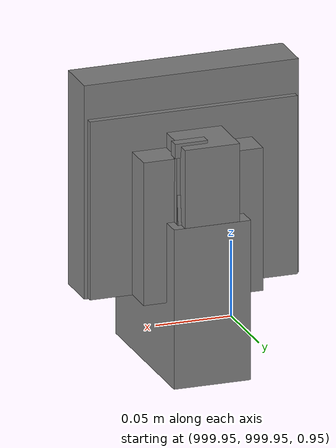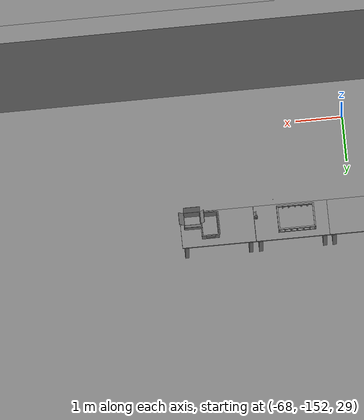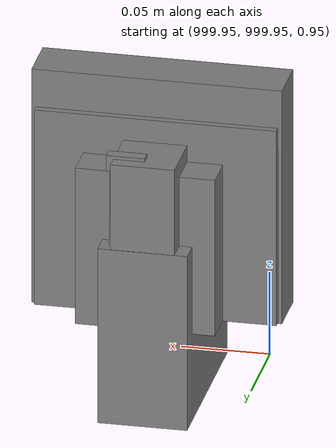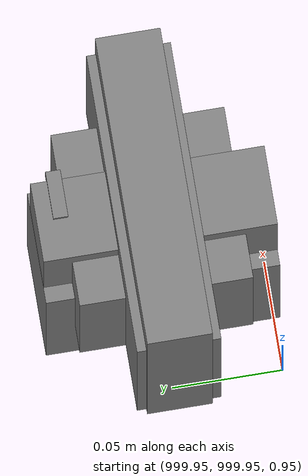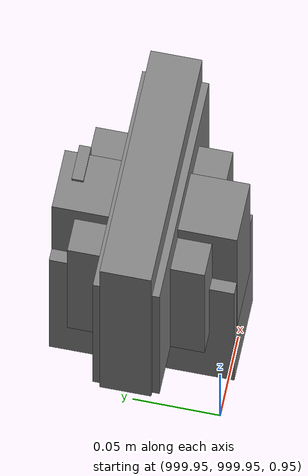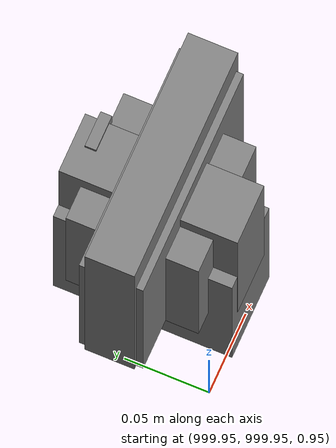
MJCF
<mujoco>
    <option gravity="0.000000000 0.000000000 -9.810000420" timestep="0.0049999999" integrator="implicitfast" density="1.225" viscosity="1.8000001e-05" noslip_iterations="10" iterations="100" sdf_iterations="50">
        <flag multiccd="disable"/>
    </option>
    <size memory="1000M"/>
    <compiler coordinate="local"/>
    <worldbody>
        <light cutoff="30" pos="0 1 1" dir="0 -1 -2"/>
        <light cutoff="30" pos="0 -1 1" dir="0 1 -2"/>
        <body pos="1000.000000000 1000.000000000 1.000000000" euler="0.000011953 0.000005123 -179.999984741" name="openloong_gripper_2f85_fix_base_usda_intel_box">
            <geom contype="1" conaffinity="1" density="1000" type="box" material="" rgba="0.500000000 0.500000000 0.500000000 1.000000000" solimp="0.899999976 0.949999988 0.001000000" friction="1.000000000 0.005000000 0.000100000" solref="0.020000000 1.000000000" margin="0" condim="3" group="0" pos="0.000000000 -0.000067139 0.000082284" quat="0.707106709 0.000000225 0.000000253 0.707106650" size="0.052800003 0.025300000 0.052800003" name="openloong_gripper_2f85_fix_base_usda_geom_60747510_BBAF_45A8_B33D_A471C51DF48C"/>
            <freejoint name="openloong_gripper_2f85_fix_base_usda_intel_box_joint"/>
            <site size="0.005000000 0.005000000 0.005000000" rgba="0.500000000 0.500000000 0.500000000 1.000000000" pos="0.000000000 0.000000000 0.000000000" quat="0.999961913 0.008726500 0.000000000 0.000000000" group="0" type="sphere" name="openloong_gripper_2f85_fix_base_usda_intel_boxsite"/>
        </body>
        <body pos="-66.135269165 -149.701232910 31.166938782" euler="155.268280029 11.286277771 -23.558074951" mocap="true" name="spotlight1_SpotLight"/>
        <body pos="1000.000000000 999.999938965 1.000000000" euler="0.000000000 0.000000000 180.000000000" name="openloong_gripper_2f85_fix_base_usda_intelcore_i5">
            <geom contype="1" conaffinity="1" density="1000" type="box" material="" rgba="0.500000000 0.500000000 0.500000000 1.000000000" solimp="0.899999976 0.949999988 0.001000000" friction="1.000000000 0.005000000 0.000100000" solref="0.020000000 1.000000000" margin="0" condim="3" group="0" pos="0.000000000 0.000000000 0.051722717" quat="0.707106709 0.000000000 0.000000000 -0.707106769" size="0.052800000 0.018080002 0.052800000" name="openloong_gripper_2f85_fix_base_usda_geom_885F4C3E_F90B_4CAF_B076_319E65455F6E"/>
            <freejoint name="openloong_gripper_2f85_fix_base_usda_intelcore_i5_joint"/>
            <site size="0.005000000 0.005000000 0.005000000" rgba="0.500000000 0.500000000 0.500000000 1.000000000" pos="0.000000000 0.000000000 0.000000000" quat="0.999961913 0.008726534 0.000000000 0.000000000" group="0" type="sphere" name="openloong_gripper_2f85_fix_base_usda_intelcore_i5site"/>
        </body>
        <body pos="1000.000000000 1000.000000000 1.000000000" euler="0.000000000 0.000000000 180.000000000" name="openloong_gripper_2f85_fix_base_usda_wifi_box">
            <geom contype="1" conaffinity="1" density="1000" type="box" material="" rgba="0.500000000 0.500000000 0.500000000 1.000000000" solimp="0.899999976 0.949999988 0.001000000" friction="1.000000000 0.005000000 0.000100000" solref="0.020000000 1.000000000" margin="0" condim="3" group="0" pos="0.000000000 0.000000000 0.058978677" quat="0.000000000 0.000000047 0.000000000 1.000000000" size="0.068499997 0.018999999 0.059000000" name="openloong_gripper_2f85_fix_base_usda_geom_18641014_E9A2_4D74_A9E8_A6DB111473E5"/>
            <freejoint name="openloong_gripper_2f85_fix_base_usda_wifi_box_joint"/>
            <site size="0.005000000 0.005000000 0.005000000" rgba="0.500000000 0.500000000 0.500000000 1.000000000" pos="0.000000000 0.000000000 0.000000000" quat="0.999961913 0.008726500 0.000000000 0.000000000" group="0" type="sphere" name="openloong_gripper_2f85_fix_base_usda_wifi_boxsite"/>
        </body>
        <body pos="1000.000000000 1000.000000000 1.000000000" euler="0.000000000 0.000000000 180.000000000" name="openloong_gripper_2f85_fix_base_usda_cpu_fan">
            <geom contype="1" conaffinity="1" density="1000" type="box" material="" rgba="0.500000000 0.500000000 0.500000000 1.000000000" solimp="0.899999976 0.949999988 0.001000000" friction="1.000000000 0.005000000 0.000100000" solref="0.020000000 1.000000000" margin="0" condim="3" group="0" pos="0.000000000 0.000000000 0.070034981" quat="0.000000000 0.000000000 0.000000000 1.000000000" size="0.070700005 0.014699999 0.070700005" name="openloong_gripper_2f85_fix_base_usda_geom_89309AE4_A3A2_4F89_A443_FB3B009E90B2"/>
            <freejoint name="openloong_gripper_2f85_fix_base_usda_cpu_fan_joint"/>
            <site size="0.005000000 0.005000000 0.005000000" rgba="0.500000000 0.500000000 0.500000000 1.000000000" pos="0.000000000 0.000000000 0.000000000" quat="0.999961913 0.008726535 0.000000000 0.000000000" group="0" type="sphere" name="openloong_gripper_2f85_fix_base_usda_cpu_fancsite"/>
        </body>
        <body pos="-66.392898560 -149.314605713 31.170783997" euler="-174.348709106 -88.576530457 42.612815857" mocap="true" name="spotlight3_SpotLight"/>
        <body pos="1000.000000000 1000.000000000 1.000000000" euler="0.000000000 0.000000000 180.000000000" name="openloong_gripper_2f85_fix_base_usda_battery_01">
            <geom contype="1" conaffinity="1" density="1000" type="box" material="" rgba="0.500000000 0.500000000 0.500000000 1.000000000" solimp="0.899999976 0.949999988 0.001000000" friction="1.000000000 0.005000000 0.000100000" solref="0.020000000 1.000000000" margin="0" condim="3" group="0" pos="-0.011123657 -0.041940309 0.101691343" quat="1.000000000 0.000000000 0.000000000 0.000000000" size="0.010800000 0.003375000 0.004725000" name="openloong_gripper_2f85_fix_base_usda_geom_E894B28E_EB5B_4596_A780_1DB14E37A068"/>
            <geom contype="1" conaffinity="1" density="1000" type="box" material="" rgba="0.500000000 0.500000000 0.500000000 1.000000000" solimp="0.899999976 0.949999988 0.001000000" friction="1.000000000 0.005000000 0.000100000" solref="0.020000000 1.000000000" margin="0" condim="3" group="0" pos="-0.010876465 -0.044247437 0.047066893" quat="0.998702705 -0.050920475 0.000000000 0.000000000" size="0.009450001 0.002700000 0.024975000" name="openloong_gripper_2f85_fix_base_usda_geom_961746EA_AA62_4C81_84B9_6F0BAEA32743"/>
            <geom contype="1" conaffinity="1" density="1000" type="box" material="" rgba="0.500000000 0.500000000 0.500000000 1.000000000" solimp="0.899999976 0.949999988 0.001000000" friction="1.000000000 0.005000000 0.000100000" solref="0.020000000 1.000000000" margin="0" condim="3" group="0" pos="-0.001235962 -0.000659180 0.047381196" quat="1.000000000 0.000000000 0.000000000 0.000000000" size="0.039420001 0.039150000 0.047250003" name="openloong_gripper_2f85_fix_base_usda_geom_69BB433B_8AA4_4911_9B8F_B75D574D6C14"/>
            <geom contype="1" conaffinity="1" density="1000" type="box" material="" rgba="0.500000000 0.500000000 0.500000000 1.000000000" solimp="0.899999976 0.949999988 0.001000000" friction="1.000000000 0.005000000 0.000100000" solref="0.020000000 1.000000000" margin="0" condim="3" group="0" pos="-0.010876465 -0.039138794 0.009851727" quat="1.000000000 0.000000000 0.000000000 0.000000000" size="0.009450001 0.010800000 0.013500000" name="openloong_gripper_2f85_fix_base_usda_geom_76FCFABD_44B6_4AD7_9014_CD9805436A53"/>
            <geom contype="1" conaffinity="1" density="1000" type="box" material="" rgba="0.500000000 0.500000000 0.500000000 1.000000000" solimp="0.899999976 0.949999988 0.001000000" friction="1.000000000 0.005000000 0.000100000" solref="0.020000000 1.000000000" margin="0" condim="3" group="0" pos="-0.010876465 -0.041528322 0.071508206" quat="1.000000000 0.000000000 0.000000000 0.000000000" size="0.009450001 0.002700000 0.027000001" name="openloong_gripper_2f85_fix_base_usda_geom_59C8EC79_A397_4173_A99A_E139BDFFA0E2"/>
            <freejoint name="openloong_gripper_2f85_fix_base_usda_battery_01_joint"/>
            <site size="0.005000000 0.005000000 0.005000000" rgba="0.500000000 0.500000000 0.500000000 1.000000000" pos="0.000000000 0.000000000 0.000000000" quat="0.999961913 0.008726500 0.000000000 0.000000000" group="0" type="sphere" name="openloong_gripper_2f85_fix_base_usda_battery_01site"/>
        </body>
        <body pos="-66.395195007 -149.472183228 31.164295197" euler="104.324356079 69.430191040 -66.737266541" mocap="true" name="spotlight4_SpotLight"/>
        <body pos="-64.866622925 -149.383972168 30.183746338" euler="89.999984741 89.999946594 0.000000000" name="openloong_gripper_2f85_fix_base_usda_bluebox_01">
            <geom contype="1" conaffinity="1" density="1000" type="box" material="" rgba="0.500000000 0.500000000 0.500000000 1.000000000" solimp="0.899999976 0.949999988 0.001000000" friction="1.000000000 0.005000000 0.000100000" solref="0.020000000 1.000000000" margin="0" condim="3" group="0" pos="0.276580811 0.187225342 0.000068665" quat="0.707106948 0.000077471 0.707106352 0.000077486" size="0.100000001 0.057999998 0.010000000" name="openloong_gripper_2f85_fix_base_usda_geom_353DDC21_CA75_4A9F_9875_79048084EF30"/>
            <geom contype="1" conaffinity="1" density="1000" type="box" material="" rgba="0.500000000 0.500000000 0.500000000 1.000000000" solimp="0.899999976 0.949999988 0.001000000" friction="1.000000000 0.005000000 0.000100000" solref="0.020000000 1.000000000" margin="0" condim="3" group="0" pos="0.000000000 0.002883911 0.000000000" quat="0.999999881 0.000000000 0.000000000 0.000000000" size="0.254000008 0.003000000 0.172000006" name="openloong_gripper_2f85_fix_base_usda_geom_27EB7D2E_6B32_4EF2_92A0_1D7EBD492958"/>
            <geom contype="1" conaffinity="1" density="1000" type="box" material="" rgba="0.500000000 0.500000000 0.500000000 1.000000000" solimp="0.899999976 0.949999988 0.001000000" friction="1.000000000 0.005000000 0.000100000" solref="0.020000000 1.000000000" margin="0" condim="3" group="0" pos="0.000000000 0.124874115 0.173484802" quat="0.999796331 0.020176515 -0.000000015 0.000000030" size="0.259999990 0.119999997 0.007000000" name="openloong_gripper_2f85_fix_base_usda_geom_D45220A8_2171_4DE7_A16F_4E882ECE422E"/>
            <geom contype="1" conaffinity="1" density="1000" type="box" material="" rgba="0.500000000 0.500000000 0.500000000 1.000000000" solimp="0.899999976 0.949999988 0.001000000" friction="1.000000000 0.005000000 0.000100000" solref="0.020000000 1.000000000" margin="0" condim="3" group="0" pos="0.000000000 0.124874115 -0.173469543" quat="0.999796331 -0.020176545 -0.000000015 0.000000000" size="0.259999990 0.119999997 0.007000000" name="openloong_gripper_2f85_fix_base_usda_geom_FFDA79B3_1C24_4415_AB74_94BDC16B24B8"/>
            <geom contype="1" conaffinity="1" density="1000" type="box" material="" rgba="0.500000000 0.500000000 0.500000000 1.000000000" solimp="0.899999976 0.949999988 0.001000000" friction="1.000000000 0.005000000 0.000100000" solref="0.020000000 1.000000000" margin="0" condim="3" group="0" pos="0.000000000 0.214008331 0.188980103" quat="0.999912977 0.013176724 0.000000015 0.000000000" size="0.259999990 0.029999999 0.012500000" name="openloong_gripper_2f85_fix_base_usda_geom_A9816A4F_F2F0_4D3B_8490_32476071A4C8"/>
            <geom contype="1" conaffinity="1" density="1000" type="box" material="" rgba="0.500000000 0.500000000 0.500000000 1.000000000" solimp="0.899999976 0.949999988 0.001000000" friction="1.000000000 0.005000000 0.000100000" solref="0.020000000 1.000000000" margin="0" condim="3" group="0" pos="-0.258361816 0.125289917 0.001876831" quat="0.702796936 -0.020792112 0.710783124 0.020769298" size="0.189999998 0.119999997 0.009000000" name="openloong_gripper_2f85_fix_base_usda_geom_28643969_61FA_48CE_A0D0_E4ACDEEE5847"/>
            <geom contype="1" conaffinity="1" density="1000" type="box" material="" rgba="0.500000000 0.500000000 0.500000000 1.000000000" solimp="0.899999976 0.949999988 0.001000000" friction="1.000000000 0.005000000 0.000100000" solref="0.020000000 1.000000000" margin="0" condim="3" group="0" pos="0.000000000 0.214008331 -0.188980103" quat="0.999912977 -0.013176769 0.000000030 0.000000015" size="0.259999990 0.029999999 0.012500000" name="openloong_gripper_2f85_fix_base_usda_geom_73144BDC_821C_4A9A_8CD4_5E7D18039B51"/>
            <geom contype="1" conaffinity="1" density="1000" type="box" material="" rgba="0.500000000 0.500000000 0.500000000 1.000000000" solimp="0.899999976 0.949999988 0.001000000" friction="1.000000000 0.005000000 0.000100000" solref="0.020000000 1.000000000" margin="0" condim="3" group="0" pos="-0.276611328 0.187225342 0.000068665" quat="0.707106650 0.000077441 0.707106709 0.000077456" size="0.100000001 0.057999998 0.010000000" name="openloong_gripper_2f85_fix_base_usda_geom_560E75C4_E2DE_4A4C_BC01_B32A8299841F"/>
            <geom contype="1" conaffinity="1" density="1000" type="box" material="" rgba="0.500000000 0.500000000 0.500000000 1.000000000" solimp="0.899999976 0.949999988 0.001000000" friction="1.000000000 0.005000000 0.000100000" solref="0.020000000 1.000000000" margin="0" condim="3" group="0" pos="0.258331299 0.125289917 0.001876831" quat="0.702851415 0.018856421 0.710823774 -0.019329369" size="0.189999998 0.119999997 0.009000000" name="openloong_gripper_2f85_fix_base_usda_geom_FB741874_9581_4FC7_AA8D_F089D1C78A8C"/>
            <freejoint name="openloong_gripper_2f85_fix_base_usda_bluebox_01_joint"/>
            <site size="0.005000000 0.005000000 0.005000000" rgba="0.500000000 0.500000000 0.500000000 1.000000000" pos="0.000000000 0.000000000 0.000000000" quat="0.999961913 0.008726534 0.000000000 0.000000000" group="0" type="sphere" name="openloong_gripper_2f85_fix_base_usda_bluebox_01site"/>
        </body>
        <body pos="-64.496299744 -149.491867065 30.235729218" euler="0.000000000 0.000000000 89.999946594" name="openloong_gripper_2f85_fix_base_usda_cardboardbox_01">
            <geom contype="1" conaffinity="1" density="1000" type="box" material="" rgba="0.500000000 0.500000000 0.500000000 1.000000000" solimp="0.899999976 0.949999988 0.001000000" friction="1.000000000 0.005000000 0.000100000" solref="0.020000000 1.000000000" margin="0" condim="3" group="0" pos="-0.003166199 -0.004086494 0.005052090" quat="1.000000000 0.000000000 0.000000000 0.000000000" size="0.142499998 0.177500010 0.005000000" name="openloong_gripper_2f85_fix_base_usda_geom_00A957C3_828C_42F5_9411_573CD1F88EC8"/>
            <geom contype="1" conaffinity="1" density="1000" type="box" material="" rgba="0.500000000 0.500000000 0.500000000 1.000000000" solimp="0.899999976 0.949999988 0.001000000" friction="1.000000000 0.005000000 0.000100000" solref="0.020000000 1.000000000" margin="0" condim="3" group="0" pos="-0.003166199 0.170316696 0.150570869" quat="1.000000000 0.000000000 0.000000000 0.000000000" size="0.142499998 0.005000000 0.149999991" name="openloong_gripper_2f85_fix_base_usda_geom_01673788_B318_4D06_BE27_9B0FF70CAE4D"/>
            <geom contype="1" conaffinity="1" density="1000" type="box" material="" rgba="0.500000000 0.500000000 0.500000000 1.000000000" solimp="0.899999976 0.949999988 0.001000000" friction="1.000000000 0.005000000 0.000100000" solref="0.020000000 1.000000000" margin="0" condim="3" group="0" pos="-0.147399902 -0.005307198 0.150570869" quat="1.000000000 0.000000000 0.000000000 0.000000000" size="0.005000000 0.177500010 0.149999991" name="openloong_gripper_2f85_fix_base_usda_geom_D82F9D29_A531_429F_8746_C58345F71AB0"/>
            <geom contype="1" conaffinity="1" density="1000" type="box" material="" rgba="0.500000000 0.500000000 0.500000000 1.000000000" solimp="0.899999976 0.949999988 0.001000000" friction="1.000000000 0.005000000 0.000100000" solref="0.020000000 1.000000000" margin="0" condim="3" group="0" pos="0.140275955 -0.005307198 0.150570869" quat="1.000000000 0.000000000 0.000000000 0.000000000" size="0.005000000 0.177500010 0.149999991" name="openloong_gripper_2f85_fix_base_usda_geom_33373082_AA20_46D4_8D86_AE07EE79EA51"/>
            <geom contype="1" conaffinity="1" density="1000" type="box" material="" rgba="0.500000000 0.500000000 0.500000000 1.000000000" solimp="0.899999976 0.949999988 0.001000000" friction="1.000000000 0.005000000 0.000100000" solref="0.020000000 1.000000000" margin="0" condim="3" group="0" pos="-0.003166199 -0.181550980 0.150570869" quat="1.000000000 0.000000000 0.000000000 0.000000000" size="0.142499998 0.005000000 0.149999991" name="openloong_gripper_2f85_fix_base_usda_geom_D912FE7A_271A_4746_94F5_4F9C1879F39A"/>
            <freejoint name="openloong_gripper_2f85_fix_base_usda_cardboardbox_01_joint"/>
            <site size="0.005000000 0.005000000 0.005000000" rgba="0.500000000 0.500000000 0.500000000 1.000000000" pos="0.000000000 0.000000000 0.000000000" quat="0.999961913 0.008726535 0.000000000 0.000000000" group="0" type="sphere" name="openloong_gripper_2f85_fix_base_usda_site_EB539425_1B6B_490C_A3B4_D958C65D183A"/>
            <body pos="0.139160156 -0.004048347 0.301930904" euler="-179.999954224 49.383502960 179.999954224" name="openloong_gripper_2f85_fix_base_usda_A1_006">
                <geom contype="1" conaffinity="1" density="1000" type="box" material="" rgba="0.500000000 0.500000000 0.500000000 1.000000000" solimp="0.899999976 0.949999988 0.001000000" friction="1.000000000 0.005000000 0.000100000" solref="0.020000000 1.000000000" margin="0" condim="3" group="0" pos="-0.071587563 0.000009537 0.001745224" quat="0.999999881 0.000000000 0.000000000 0.000000000" size="0.071249999 0.179999992 0.002500000" name="openloong_gripper_2f85_fix_base_usda_geom_2560E4EB_B906_4654_88F4_B331AF68F96E"/>
                <joint armature="0" stiffness="0.07" damping="0.0099999998" axis="0.000000 1.000000 0.000000" type="hinge" name="openloong_gripper_2f85_fix_base_usda_A1_006"/>
            </body>
            <body pos="-0.145902634 -0.004086494 0.301938057" euler="-180.000000000 -60.000011444 -180.000000000" name="openloong_gripper_2f85_fix_base_usda_A2_006">
                <geom contype="1" conaffinity="1" density="1000" type="box" material="" rgba="0.500000000 0.500000000 0.500000000 1.000000000" solimp="0.899999976 0.949999988 0.001000000" friction="1.000000000 0.005000000 0.000100000" solref="0.020000000 1.000000000" margin="0" condim="3" group="0" pos="0.071268082 0.000009537 0.002717972" quat="0.000002921 0.000000000 -0.000000030 0.999999881" size="0.071249999 0.179999992 0.002500000" name="openloong_gripper_2f85_fix_base_usda_geom_5D20494A_1CA3_4E20_AC1D_94B69C932B1B"/>
                <joint armature="0" stiffness="0.07" damping="0.0099999998" axis="0.000000 1.000000 0.000000" type="hinge" name="openloong_gripper_2f85_fix_base_usda_A2_006"/>
            </body>
            <body pos="-0.003385544 0.175991058 0.301930904" euler="-125.858116150 -0.000004561 0.000002331" name="openloong_gripper_2f85_fix_base_usda_B2_006">
                <geom contype="1" conaffinity="1" density="1000" type="box" material="" rgba="0.500000000 0.500000000 0.500000000 1.000000000" solimp="0.899999976 0.949999988 0.001000000" friction="1.000000000 0.005000000 0.000100000" solref="0.020000000 1.000000000" margin="0" condim="3" group="0" pos="0.000009537 -0.070939064 -0.002470016" quat="0.999614120 0.027776197 -0.000000015 0.000000030" size="0.137500003 0.064999998 0.005000000" name="openloong_gripper_2f85_fix_base_usda_geom_AD2B5B83_91EE_4B49_8C4C_16E326BED3B4"/>
                <joint armature="0" stiffness="0.07" damping="0.0099999998" axis="1.000000 0.000000 0.000000" type="hinge" name="openloong_gripper_2f85_fix_base_usda_B2_006"/>
            </body>
            <body pos="-0.003385544 -0.184140205 0.301938057" euler="147.805557251 0.000000000 0.000000000" name="openloong_gripper_2f85_fix_base_usda_B1_006">
                <geom contype="1" conaffinity="1" density="1000" type="box" material="" rgba="0.500000000 0.500000000 0.500000000 1.000000000" solimp="0.899999976 0.949999988 0.001000000" friction="1.000000000 0.005000000 0.000100000" solref="0.020000000 1.000000000" margin="0" condim="3" group="0" pos="-0.000028610 0.070202351 -0.002703667" quat="0.999614179 -0.027776167 0.000000000 0.000000000" size="0.137500003 0.064999998 0.005000000" name="openloong_gripper_2f85_fix_base_usda_geom_A513DE10_DD45_42B8_9D6D_EBF34A133487"/>
                <joint armature="0" stiffness="0.07" damping="0.0099999998" axis="1.000000 0.000000 0.000000" type="hinge" name="openloong_gripper_2f85_fix_base_usda_B1_006"/>
            </body>
        </body>
        <body pos="-65.882858276 -149.481979370 30.229999542" euler="-64.487716675 0.000000000 0.000000000" name="openloong_gripper_2f85_fix_base_usda_Barcode">
            <geom contype="1" conaffinity="1" density="1000" type="box" material="" rgba="0.500000000 0.500000000 0.500000000 1.000000000" solimp="0.899999976 0.949999988 0.001000000" friction="1.000000000 0.005000000 0.000100000" solref="0.020000000 1.000000000" margin="0" condim="3" group="0" pos="0.000000000 0.013038635 0.001419067" quat="0.000000000 0.000000000 0.000000000 1.000000119" size="0.034000002 0.010000000 0.017999999" name="openloong_gripper_2f85_fix_base_usda_geom_75DB5AFD_87B9_4F8C_B07C_DDD2E5986106"/>
            <geom contype="1" conaffinity="1" density="1000" type="box" material="" rgba="0.500000000 0.500000000 0.500000000 1.000000000" solimp="0.899999976 0.949999988 0.001000000" friction="1.000000000 0.005000000 0.000100000" solref="0.020000000 1.000000000" margin="0" condim="3" group="0" pos="0.000000000 -0.035301208 -0.007095337" quat="0.000000000 0.000000000 -0.043619365 0.999048233" size="0.028999999 0.010000000 0.020000000" name="openloong_gripper_2f85_fix_base_usda_geom_7CB97FC6_912C_40D0_A7AE_DA01CC384EA3"/>
            <geom contype="1" conaffinity="1" density="1000" type="box" material="" rgba="0.500000000 0.500000000 0.500000000 1.000000000" solimp="0.899999976 0.949999988 0.001000000" friction="1.000000000 0.005000000 0.000100000" solref="0.020000000 1.000000000" margin="0" condim="3" group="0" pos="0.000000000 -0.043411255 -0.011749268" quat="0.922262907 0.386563420 0.000000000 0.000000000" size="0.026000001 0.010000000 0.020000000" name="openloong_gripper_2f85_fix_base_usda_geom_4A9AAACE_F826_4462_A6E2_9C5D40A11468"/>
            <geom contype="1" conaffinity="1" density="1000" type="box" material="" rgba="0.500000000 0.500000000 0.500000000 1.000000000" solimp="0.899999976 0.949999988 0.001000000" friction="1.000000000 0.005000000 0.000100000" solref="0.020000000 1.000000000" margin="0" condim="3" group="0" pos="0.000000000 -0.016967773 -0.031860352" quat="0.000000000 0.000000000 0.000000000 1.000000119" size="0.008000000 0.010000000 0.013000000" name="openloong_gripper_2f85_fix_base_usda_geom_8B50BC27_A99D_44A1_BEE2_82A3C2CE4418"/>
            <geom contype="1" conaffinity="1" density="1000" type="box" material="" rgba="0.500000000 0.500000000 0.500000000 1.000000000" solimp="0.899999976 0.949999988 0.001000000" friction="1.000000000 0.005000000 0.000100000" solref="0.020000000 1.000000000" margin="0" condim="3" group="0" pos="0.000000000 -0.001869202 0.000312805" quat="0.953716993 0.300705761 0.000000000 0.000000000" size="0.032000002 0.010000000 0.018999999" name="openloong_gripper_2f85_fix_base_usda_geom_5A7DFFB4_A076_4DD8_8D67_BBC693B16BCD"/>
            <geom contype="1" conaffinity="1" density="1000" type="box" material="" rgba="0.500000000 0.500000000 0.500000000 1.000000000" solimp="0.899999976 0.949999988 0.001000000" friction="1.000000000 0.005000000 0.000100000" solref="0.020000000 1.000000000" margin="0" condim="3" group="0" pos="0.000000000 -0.019531250 -0.003173828" quat="0.953716993 0.300705761 0.000000000 0.000000000" size="0.030999999 0.010000000 0.020000000" name="openloong_gripper_2f85_fix_base_usda_geom_D15E62AE_233A_49E0_AE95_A2D3BA644DE2"/>
            <geom contype="1" conaffinity="1" density="1000" type="box" material="" rgba="0.500000000 0.500000000 0.500000000 1.000000000" solimp="0.899999976 0.949999988 0.001000000" friction="1.000000000 0.005000000 0.000100000" solref="0.020000000 1.000000000" margin="0" condim="3" group="0" pos="0.000000000 -0.035301208 -0.007095337" quat="0.953716993 0.300705761 0.000000000 0.000000000" size="0.028999999 0.010000000 0.020000000" name="openloong_gripper_2f85_fix_base_usda_geom_741BFB93_8985_4EC1_B637_B6D0EB0D9F55"/>
            <geom contype="1" conaffinity="1" density="1000" type="box" material="" rgba="0.500000000 0.500000000 0.500000000 1.000000000" solimp="0.899999976 0.949999988 0.001000000" friction="1.000000000 0.005000000 0.000100000" solref="0.020000000 1.000000000" margin="0" condim="3" group="0" pos="0.000000000 -0.042617798 -0.071121216" quat="0.000000000 0.000000000 0.000000000 1.000000119" size="0.013000000 0.021000000 0.059999999" name="openloong_gripper_2f85_fix_base_usda_geom_A8A78B90_F5B8_4E58_AA18_C66B503A7A0D"/>
            <freejoint name="openloong_gripper_2f85_fix_base_usda_Barcode_joint"/>
            <site size="0.005000000 0.005000000 0.005000000" rgba="0.500000000 0.500000000 0.500000000 1.000000000" pos="0.000000000 0.000000000 0.000000000" quat="1.000000000 0.000000000 0.000000000 0.000000000" group="0" type="sphere" name="openloong_gripper_2f85_fix_base_usda_Barcode_site"/>
        </body>
        <body pos="-66.745018005 -149.392349243 30.184000015" euler="0.000000000 0.000000000 89.999946594" name="[22332927444873]_Basket_01">
            <geom contype="1" conaffinity="1" density="1000" type="box" material="" rgba="0.500000000 0.500000000 0.500000000 1.000000000" solimp="0.899999976 0.949999988 0.001000000" friction="1.000000000 0.005000000 0.000100000" solref="0.020000000 1.000000000" margin="0" condim="3" group="0" pos="-0.052425385 0.389207840 0.089787483" quat="0.707107008 0.000000000 0.000000000 0.707106411" size="0.014249999 0.014249999 0.059999999" name="[22332927444873]_geom_D3B1F10B_8A47_4D63_9024_B43FCA4CEF96"/>
            <geom contype="1" conaffinity="1" density="1000" type="box" material="" rgba="0.500000000 0.500000000 0.500000000 1.000000000" solimp="0.899999976 0.949999988 0.001000000" friction="1.000000000 0.005000000 0.000100000" solref="0.020000000 1.000000000" margin="0" condim="3" group="0" pos="0.264015198 -0.133043289 0.089787483" quat="0.707107008 0.000000000 0.000000000 0.707106411" size="0.014249999 0.014249999 0.059999999" name="[22332927444873]_geom_84D554FA_612B_44F5_8CA4_CDDA935278D7"/>
            <geom contype="1" conaffinity="1" density="1000" type="box" material="" rgba="0.500000000 0.500000000 0.500000000 1.000000000" solimp="0.899999976 0.949999988 0.001000000" friction="1.000000000 0.005000000 0.000100000" solref="0.020000000 1.000000000" margin="0" condim="3" group="0" pos="-0.264015198 -0.265548706 0.089793205" quat="0.707107008 0.000000000 0.000000000 0.707106411" size="0.014249999 0.014249999 0.059999999" name="[22332927444873]_geom_CE6CF563_9FB9_4E48_A7E4_85EA20B3277D"/>
            <geom contype="1" conaffinity="1" density="1000" type="box" material="" rgba="0.500000000 0.500000000 0.500000000 1.000000000" solimp="0.899999976 0.949999988 0.001000000" friction="1.000000000 0.005000000 0.000100000" solref="0.020000000 1.000000000" margin="0" condim="3" group="0" pos="-0.160263062 -0.389322281 0.089793205" quat="0.707107008 0.000000000 0.000000000 0.707106411" size="0.014249999 0.014249999 0.059999999" name="[22332927444873]_geom_FE7C7B21_0A52_409C_BF04_AE560FB61C76"/>
            <geom contype="1" conaffinity="1" density="1000" type="box" material="" rgba="0.500000000 0.500000000 0.500000000 1.000000000" solimp="0.899999976 0.949999988 0.001000000" friction="1.000000000 0.005000000 0.000100000" solref="0.020000000 1.000000000" margin="0" condim="3" group="0" pos="0.162265778 -0.389322281 0.089787483" quat="0.707107008 0.000000000 0.000000000 0.707106411" size="0.014249999 0.014249999 0.059999999" name="[22332927444873]_geom_F287BE5F_E305_4BE3_A88D_706547FDA5B0"/>
            <geom contype="1" conaffinity="1" density="1000" type="box" material="" rgba="0.500000000 0.500000000 0.500000000 1.000000000" solimp="0.899999976 0.949999988 0.001000000" friction="1.000000000 0.005000000 0.000100000" solref="0.020000000 1.000000000" margin="0" condim="3" group="0" pos="0.264015198 0.389207840 0.089787483" quat="0.707107008 0.000000000 0.000000000 0.707106411" size="0.014249999 0.014249999 0.059999999" name="[22332927444873]_geom_351A999C_80D5_4C02_ABFF_CBA244FC6C4A"/>
            <geom contype="1" conaffinity="1" density="1000" type="box" material="" rgba="0.500000000 0.500000000 0.500000000 1.000000000" solimp="0.899999976 0.949999988 0.001000000" friction="1.000000000 0.005000000 0.000100000" solref="0.020000000 1.000000000" margin="0" condim="3" group="0" pos="-0.264015198 -0.133043289 0.089793205" quat="0.707107008 0.000000000 0.000000000 0.707106411" size="0.014249999 0.014249999 0.059999999" name="[22332927444873]_geom_654DAE29_2851_431E_8C58_25701B60DAE0"/>
            <geom contype="1" conaffinity="1" density="1000" type="box" material="" rgba="0.500000000 0.500000000 0.500000000 1.000000000" solimp="0.899999976 0.949999988 0.001000000" friction="1.000000000 0.005000000 0.000100000" solref="0.020000000 1.000000000" margin="0" condim="3" group="0" pos="-0.264026642 0.269256592 0.089793205" quat="0.707107008 0.000000000 0.000000000 0.707106411" size="0.014249999 0.014249999 0.059999999" name="[22332927444873]_geom_1628E923_5D69_4803_A026_AAB8A28D949B"/>
            <geom contype="1" conaffinity="1" density="1000" type="box" material="" rgba="0.500000000 0.500000000 0.500000000 1.000000000" solimp="0.899999976 0.949999988 0.001000000" friction="1.000000000 0.005000000 0.000100000" solref="0.020000000 1.000000000" margin="0" condim="3" group="0" pos="0.054462433 0.389207840 0.089787483" quat="0.707107008 0.000000000 0.000000000 0.707106411" size="0.014249999 0.014249999 0.059999999" name="[22332927444873]_geom_AEB7C72E_408D_4A2D_A9F0_213F024A3F94"/>
            <geom contype="1" conaffinity="1" density="1000" type="box" material="" rgba="0.500000000 0.500000000 0.500000000 1.000000000" solimp="0.899999976 0.949999988 0.001000000" friction="1.000000000 0.005000000 0.000100000" solref="0.020000000 1.000000000" margin="0" condim="3" group="0" pos="0.054462433 -0.389322281 0.089787483" quat="0.707107008 0.000000000 0.000000000 0.707106411" size="0.014249999 0.014249999 0.059999999" name="[22332927444873]_geom_20FEE360_B398_4D94_A5E3_47841999A1B9"/>
            <geom contype="1" conaffinity="1" density="1000" type="box" material="" rgba="0.500000000 0.500000000 0.500000000 1.000000000" solimp="0.899999976 0.949999988 0.001000000" friction="1.000000000 0.005000000 0.000100000" solref="0.020000000 1.000000000" margin="0" condim="3" group="0" pos="0.264015198 0.269256592 0.089793205" quat="0.707107008 0.000000000 0.000000000 0.707106411" size="0.014249999 0.014249999 0.059999999" name="[22332927444873]_geom_CECEB7AB_E6BC_4D2C_B0B7_2337A89FE63C"/>
            <geom contype="1" conaffinity="1" density="1000" type="box" material="" rgba="0.500000000 0.500000000 0.500000000 1.000000000" solimp="0.899999976 0.949999988 0.001000000" friction="1.000000000 0.005000000 0.000100000" solref="0.020000000 1.000000000" margin="0" condim="3" group="0" pos="0.264015198 -0.389322281 0.089787483" quat="0.707107008 0.000000000 0.000000000 0.707106411" size="0.014249999 0.014249999 0.059999999" name="[22332927444873]_geom_12264AAF_B523_4BA3_9D7D_0B43E2643D13"/>
            <geom contype="1" conaffinity="1" density="1000" type="box" material="" rgba="0.500000000 0.500000000 0.500000000 1.000000000" solimp="0.899999976 0.949999988 0.001000000" friction="1.000000000 0.005000000 0.000100000" solref="0.020000000 1.000000000" margin="0" condim="3" group="0" pos="0.000000000 0.000000000 0.015998840" quat="0.707107008 0.000000000 0.000000000 0.707106411" size="0.403499991 0.279000014 0.015750000" name="[22332927444873]_geom_C4EA5ABE_C52A_4A2F_B690_EA49D2B0156F"/>
            <geom contype="1" conaffinity="1" density="1000" type="box" material="" rgba="0.500000000 0.500000000 0.500000000 1.000000000" solimp="0.899999976 0.949999988 0.001000000" friction="1.000000000 0.005000000 0.000100000" solref="0.020000000 1.000000000" margin="0" condim="3" group="0" pos="0.000000000 -0.389476776 0.163619041" quat="0.707107008 0.000000000 0.000000000 0.707106411" size="0.015000000 0.277500004 0.015750000" name="[22332927444873]_geom_3D036891_F7C5_4DEF_B83B_2D6971FC9536"/>
            <geom contype="1" conaffinity="1" density="1000" type="box" material="" rgba="0.500000000 0.500000000 0.500000000 1.000000000" solimp="0.899999976 0.949999988 0.001000000" friction="1.000000000 0.005000000 0.000100000" solref="0.020000000 1.000000000" margin="0" condim="3" group="0" pos="0.162265778 0.389207840 0.089787483" quat="0.707107008 0.000000000 0.000000000 0.707106411" size="0.014249999 0.014249999 0.059999999" name="[22332927444873]_geom_1D57283B_8DA2_467D_97DD_F3CB0962F027"/>
            <geom contype="1" conaffinity="1" density="1000" type="box" material="" rgba="0.500000000 0.500000000 0.500000000 1.000000000" solimp="0.899999976 0.949999988 0.001000000" friction="1.000000000 0.005000000 0.000100000" solref="0.020000000 1.000000000" margin="0" condim="3" group="0" pos="0.000000000 0.389471054 0.163619041" quat="0.707107008 0.000000000 0.000000000 0.707106411" size="0.015000000 0.277500004 0.015750000" name="[22332927444873]_geom_C7131A31_4743_4BCB_AE05_7AEB51781D49"/>
            <geom contype="1" conaffinity="1" density="1000" type="box" material="" rgba="0.500000000 0.500000000 0.500000000 1.000000000" solimp="0.899999976 0.949999988 0.001000000" friction="1.000000000 0.005000000 0.000100000" solref="0.020000000 1.000000000" margin="0" condim="3" group="0" pos="-0.263511658 0.000000000 0.163619041" quat="0.707107008 0.000000000 0.000000000 0.707106411" size="0.403499991 0.015000000 0.015750000" name="[22332927444873]_geom_540F747F_B982_4A5E_9A63_3D80A7B92EBA"/>
            <geom contype="1" conaffinity="1" density="1000" type="box" material="" rgba="0.500000000 0.500000000 0.500000000 1.000000000" solimp="0.899999976 0.949999988 0.001000000" friction="1.000000000 0.005000000 0.000100000" solref="0.020000000 1.000000000" margin="0" condim="3" group="0" pos="-0.264015198 0.141334534 0.089793205" quat="0.707107008 0.000000000 0.000000000 0.707106411" size="0.014249999 0.014249999 0.059999999" name="[22332927444873]_geom_AAE75A9B_3DD3_4A38_A913_B599DA96E26E"/>
            <geom contype="1" conaffinity="1" density="1000" type="box" material="" rgba="0.500000000 0.500000000 0.500000000 1.000000000" solimp="0.899999976 0.949999988 0.001000000" friction="1.000000000 0.005000000 0.000100000" solref="0.020000000 1.000000000" margin="0" condim="3" group="0" pos="0.264015198 -0.265548706 0.089787483" quat="0.707107008 0.000000000 0.000000000 0.707106411" size="0.014249999 0.014249999 0.059999999" name="[22332927444873]_geom_77F90AC3_0681_407C_AE69_B3932ED27B52"/>
            <geom contype="1" conaffinity="1" density="1000" type="box" material="" rgba="0.500000000 0.500000000 0.500000000 1.000000000" solimp="0.899999976 0.949999988 0.001000000" friction="1.000000000 0.005000000 0.000100000" solref="0.020000000 1.000000000" margin="0" condim="3" group="0" pos="-0.160263062 0.389207840 0.089787483" quat="0.707107008 0.000000000 0.000000000 0.707106411" size="0.014249999 0.014249999 0.059999999" name="[22332927444873]_geom_0962854E_6C18_45E3_AA72_CB4C7E59062E"/>
            <geom contype="1" conaffinity="1" density="1000" type="box" material="" rgba="0.500000000 0.500000000 0.500000000 1.000000000" solimp="0.899999976 0.949999988 0.001000000" friction="1.000000000 0.005000000 0.000100000" solref="0.020000000 1.000000000" margin="0" condim="3" group="0" pos="-0.052425385 -0.389322281 0.089787483" quat="0.707107008 0.000000000 0.000000000 0.707106411" size="0.014249999 0.014249999 0.059999999" name="[22332927444873]_geom_16025C03_6D3D_41C2_9E56_A2A5FA04FDF6"/>
            <geom contype="1" conaffinity="1" density="1000" type="box" material="" rgba="0.500000000 0.500000000 0.500000000 1.000000000" solimp="0.899999976 0.949999988 0.001000000" friction="1.000000000 0.005000000 0.000100000" solref="0.020000000 1.000000000" margin="0" condim="3" group="0" pos="-0.264026642 -0.389322281 0.089793205" quat="0.707107008 0.000000000 0.000000000 0.707106411" size="0.014249999 0.014249999 0.059999999" name="[22332927444873]_geom_A6AE790A_6281_4840_80C9_CED618DBEC74"/>
            <geom contype="1" conaffinity="1" density="1000" type="box" material="" rgba="0.500000000 0.500000000 0.500000000 1.000000000" solimp="0.899999976 0.949999988 0.001000000" friction="1.000000000 0.005000000 0.000100000" solref="0.020000000 1.000000000" margin="0" condim="3" group="0" pos="0.264015198 0.141334534 0.089787483" quat="0.707107008 0.000000000 0.000000000 0.707106411" size="0.014249999 0.014249999 0.059999999" name="[22332927444873]_geom_1B17E37F_C715_452D_9771_DE9FB6AFA955"/>
            <geom contype="1" conaffinity="1" density="1000" type="box" material="" rgba="0.500000000 0.500000000 0.500000000 1.000000000" solimp="0.899999976 0.949999988 0.001000000" friction="1.000000000 0.005000000 0.000100000" solref="0.020000000 1.000000000" margin="0" condim="3" group="0" pos="-0.264015198 0.389207840 0.089793205" quat="0.707107008 0.000000000 0.000000000 0.707106411" size="0.014249999 0.014249999 0.059999999" name="[22332927444873]_geom_F5E928AC_9379_44F1_8060_11884BAD2F2C"/>
            <geom contype="1" conaffinity="1" density="1000" type="box" material="" rgba="0.500000000 0.500000000 0.500000000 1.000000000" solimp="0.899999976 0.949999988 0.001000000" friction="1.000000000 0.005000000 0.000100000" solref="0.020000000 1.000000000" margin="0" condim="3" group="0" pos="0.264015198 0.004480362 0.089787483" quat="0.707107008 0.000000000 0.000000000 0.707106411" size="0.014249999 0.014249999 0.059999999" name="[22332927444873]_geom_2F43F025_0054_4552_BE51_672CB499D049"/>
            <geom contype="1" conaffinity="1" density="1000" type="box" material="" rgba="0.500000000 0.500000000 0.500000000 1.000000000" solimp="0.899999976 0.949999988 0.001000000" friction="1.000000000 0.005000000 0.000100000" solref="0.020000000 1.000000000" margin="0" condim="3" group="0" pos="0.263694763 -0.000011444 0.163619041" quat="0.707107008 0.000000000 0.000000000 0.707106411" size="0.403499991 0.015000000 0.015750000" name="[22332927444873]_geom_E5C662CF_8DD0_4F21_8056_00860B587B36"/>
            <geom contype="1" conaffinity="1" density="1000" type="box" material="" rgba="0.500000000 0.500000000 0.500000000 1.000000000" solimp="0.899999976 0.949999988 0.001000000" friction="1.000000000 0.005000000 0.000100000" solref="0.020000000 1.000000000" margin="0" condim="3" group="0" pos="-0.264015198 0.004480362 0.089793205" quat="0.707107008 0.000000000 0.000000000 0.707106411" size="0.014249999 0.014249999 0.059999999" name="[22332927444873]_geom_A0B66B61_0F46_409A_82F7_477053A03C15"/>
            <freejoint name="[22332927444873]_joint_8790DD2E_BA7B_4B12_9512_CC07227741BE"/>
        </body>
        <body pos="0.000000000 0.000000000 0.000000000" euler="0.000000000 0.000000000 0.000000000" name="Static Objects_Static Objects">
            <geom contype="1" conaffinity="1" density="1000" type="box" material="" rgba="0.500000000 0.500000000 0.500000000 1.000000000" solimp="0.899999976 0.949999988 0.001000000" friction="1.000000000 0.005000000 0.000100000" solref="0.020000000 1.000000000" margin="0" condim="3" group="0" pos="-67.544113159 -149.365814209 29.727830887" quat="0.500000417 0.499999970 0.499999553 0.499999970" size="0.381000012 0.319999993 0.041000001" name="Static Objects_geom_6F56A718_4883_42A9_80FE_73315C961C6D"/>
            <geom contype="1" conaffinity="1" density="1000" type="box" material="" rgba="0.500000000 0.500000000 0.500000000 1.000000000" solimp="0.899999976 0.949999988 0.001000000" friction="1.000000000 0.005000000 0.000100000" solref="0.020000000 1.000000000" margin="0" condim="3" group="0" pos="-68.239501953 -149.365814209 30.086868286" quat="0.500000417 0.499999970 0.499999553 0.499999970" size="0.370999992 0.039500002 0.745000005" name="Static Objects_geom_E6E5EEB2_7114_41A0_B426_360E202C2D7D"/>
            <geom contype="1" conaffinity="1" density="1000" type="box" material="" rgba="0.500000000 0.500000000 0.500000000 1.000000000" solimp="0.899999976 0.949999988 0.001000000" friction="1.000000000 0.005000000 0.000100000" solref="0.020000000 1.000000000" margin="0" condim="3" group="0" pos="-68.239501953 -149.365814209 30.147235870" quat="0.500000417 0.499999970 0.499999553 0.499999970" size="0.400000006 0.022000000 0.800000012" name="Static Objects_geom_373BD984_C647_40AE_8D4D_C8F6F1A03052"/>
            <geom contype="1" conaffinity="1" density="1000" type="box" material="" rgba="0.500000000 0.500000000 0.500000000 1.000000000" solimp="0.899999976 0.949999988 0.001000000" friction="1.000000000 0.005000000 0.000100000" solref="0.020000000 1.000000000" margin="0" condim="3" group="0" pos="-68.934890747 -149.365814209 29.727830887" quat="0.500000417 0.499999970 0.499999553 0.499999970" size="0.381000012 0.319999993 0.041000001" name="Static Objects_geom_8C1E6CBA_D9DB_43AD_9CC9_AC369B2DEB8C"/>
            <geom contype="1" conaffinity="1" density="1000" type="box" material="" rgba="0.500000000 0.500000000 0.500000000 1.000000000" solimp="0.899999976 0.949999988 0.001000000" friction="1.000000000 0.005000000 0.000100000" solref="0.020000000 1.000000000" margin="0" condim="3" group="0" pos="-68.239501953 -149.365814209 29.561563492" quat="0.500000417 0.499999970 0.499999553 0.499999970" size="0.020000000 0.022000000 0.660000026" name="Static Objects_geom_7CBE7414_6A06_470D_B530_BC6F0CA36582"/>
            <geom contype="1" conaffinity="1" density="1000" type="box" material="" rgba="0.500000000 0.500000000 0.500000000 1.000000000" solimp="0.899999976 0.949999988 0.001000000" friction="1.000000000 0.005000000 0.000100000" solref="0.020000000 1.000000000" margin="0" condim="3" group="0" pos="-65.945671082 -149.365814209 29.727830887" quat="0.500000417 0.499999970 0.499999553 0.499999970" size="0.381000012 0.319999993 0.041000001" name="Static Objects_geom_B1AC70D1_5615_41FC_B81D_32ECD8E7636E"/>
            <geom contype="1" conaffinity="1" density="1000" type="box" material="" rgba="0.500000000 0.500000000 0.500000000 1.000000000" solimp="0.899999976 0.949999988 0.001000000" friction="1.000000000 0.005000000 0.000100000" solref="0.020000000 1.000000000" margin="0" condim="3" group="0" pos="-66.641059875 -149.365814209 30.086868286" quat="0.500000417 0.499999970 0.499999553 0.499999970" size="0.370999992 0.039500002 0.745000005" name="Static Objects_geom_F15570E5_AAA8_4EBF_9BE0_27AC5A561F0D"/>
            <geom contype="1" conaffinity="1" density="1000" type="box" material="" rgba="0.500000000 0.500000000 0.500000000 1.000000000" solimp="0.899999976 0.949999988 0.001000000" friction="1.000000000 0.005000000 0.000100000" solref="0.020000000 1.000000000" margin="0" condim="3" group="0" pos="-66.641059875 -149.365814209 30.147235870" quat="0.500000417 0.499999970 0.499999553 0.499999970" size="0.400000006 0.022000000 0.800000012" name="Static Objects_geom_D3991079_BAFD_4186_A364_07235A9361E1"/>
            <geom contype="1" conaffinity="1" density="1000" type="box" material="" rgba="0.500000000 0.500000000 0.500000000 1.000000000" solimp="0.899999976 0.949999988 0.001000000" friction="1.000000000 0.005000000 0.000100000" solref="0.020000000 1.000000000" margin="0" condim="3" group="0" pos="-67.336448669 -149.365814209 29.727830887" quat="0.500000417 0.499999970 0.499999553 0.499999970" size="0.381000012 0.319999993 0.041000001" name="Static Objects_geom_17E2511E_9B59_43A1_9B49_8E8DEC3E63CA"/>
            <geom contype="1" conaffinity="1" density="1000" type="box" material="" rgba="0.500000000 0.500000000 0.500000000 1.000000000" solimp="0.899999976 0.949999988 0.001000000" friction="1.000000000 0.005000000 0.000100000" solref="0.020000000 1.000000000" margin="0" condim="3" group="0" pos="-66.641059875 -149.365814209 29.561563492" quat="0.500000417 0.499999970 0.499999553 0.499999970" size="0.020000000 0.022000000 0.660000026" name="Static Objects_geom_89E90DDC_D91C_423B_A3B1_4D23BB948B22"/>
            <geom contype="1" conaffinity="1" density="1000" type="box" material="" rgba="0.500000000 0.500000000 0.500000000 1.000000000" solimp="0.899999976 0.949999988 0.001000000" friction="1.000000000 0.005000000 0.000100000" solref="0.020000000 1.000000000" margin="0" condim="3" group="0" pos="-64.338577271 -149.365814209 29.727830887" quat="0.500000417 0.499999970 0.499999553 0.499999970" size="0.381000012 0.319999993 0.041000001" name="Static Objects_geom_2476E5CB_34E4_47F1_AEFC_EE52ADF8E85F"/>
            <geom contype="1" conaffinity="1" density="1000" type="box" material="" rgba="0.500000000 0.500000000 0.500000000 1.000000000" solimp="0.899999976 0.949999988 0.001000000" friction="1.000000000 0.005000000 0.000100000" solref="0.020000000 1.000000000" margin="0" condim="3" group="0" pos="-65.033966064 -149.365814209 30.086868286" quat="0.500000417 0.499999970 0.499999553 0.499999970" size="0.370999992 0.039500002 0.745000005" name="Static Objects_geom_AAD6CDD4_CBCE_4691_B2C3_4745E0AA38EF"/>
            <geom contype="1" conaffinity="1" density="1000" type="box" material="" rgba="0.500000000 0.500000000 0.500000000 1.000000000" solimp="0.899999976 0.949999988 0.001000000" friction="1.000000000 0.005000000 0.000100000" solref="0.020000000 1.000000000" margin="0" condim="3" group="0" pos="-65.033966064 -149.365814209 30.147235870" quat="0.500000417 0.499999970 0.499999553 0.499999970" size="0.400000006 0.022000000 0.800000012" name="Static Objects_geom_BA41B0FC_D4C8_47D9_804F_53F9A79DCBA5"/>
            <geom contype="1" conaffinity="1" density="1000" type="box" material="" rgba="0.500000000 0.500000000 0.500000000 1.000000000" solimp="0.899999976 0.949999988 0.001000000" friction="1.000000000 0.005000000 0.000100000" solref="0.020000000 1.000000000" margin="0" condim="3" group="0" pos="-65.729354858 -149.365814209 29.727830887" quat="0.500000417 0.499999970 0.499999553 0.499999970" size="0.381000012 0.319999993 0.041000001" name="Static Objects_geom_9155B8E8_E0F8_41C2_8524_EFB79991446F"/>
            <geom contype="1" conaffinity="1" density="1000" type="box" material="" rgba="0.500000000 0.500000000 0.500000000 1.000000000" solimp="0.899999976 0.949999988 0.001000000" friction="1.000000000 0.005000000 0.000100000" solref="0.020000000 1.000000000" margin="0" condim="3" group="0" pos="-65.033966064 -149.365814209 29.561563492" quat="0.500000417 0.499999970 0.499999553 0.499999970" size="0.020000000 0.022000000 0.660000026" name="Static Objects_geom_4D234D72_4009_426F_8421_8CA90D9458EA"/>
            <geom contype="1" conaffinity="1" density="1000" type="box" material="" rgba="0.500000000 0.500000000 0.500000000 1.000000000" solimp="0.899999976 0.949999988 0.001000000" friction="1.000000000 0.005000000 0.000100000" solref="0.020000000 1.000000000" margin="0" condim="3" group="0" pos="-61.754566193 -137.853729248 33.906845093" quat="0.707107067 0.000000000 0.000000000 0.707106471" size="0.759999990 0.759999990 4.500000000" name="Static Objects_geom_2236F6D8_CC0C_4BC4_9C96_3F10CEE5E4E3"/>
            <geom contype="1" conaffinity="1" density="1000" type="box" material="" rgba="0.500000000 0.500000000 0.500000000 1.000000000" solimp="0.899999976 0.949999988 0.001000000" friction="1.000000000 0.005000000 0.000100000" solref="0.020000000 1.000000000" margin="0" condim="3" group="0" pos="-57.511135101 -144.927108765 31.707921982" quat="1.000000000 0.000000000 0.000000000 0.000000000" size="0.200000003 8.000000000 2.299999952" name="Static Objects_geom_5017C0AD_14BC_4873_827C_B00651EA26C9"/>
            <geom contype="1" conaffinity="1" density="1000" type="box" material="" rgba="0.500000000 0.500000000 0.500000000 1.000000000" solimp="0.899999976 0.949999988 0.001000000" friction="1.000000000 0.005000000 0.000100000" solref="0.020000000 1.000000000" margin="0" condim="3" group="0" pos="-80.517646790 -157.574050903 31.688196182" quat="0.707107067 0.000000000 0.000000000 0.707106471" size="0.600000024 0.600000024 2.299999952" name="Static Objects_geom_597F3FC1_AD77_4A86_AD31_9B3C0F5F1926"/>
            <geom contype="1" conaffinity="1" density="1000" type="box" material="" rgba="0.500000000 0.500000000 0.500000000 1.000000000" solimp="0.899999976 0.949999988 0.001000000" friction="1.000000000 0.005000000 0.000100000" solref="0.020000000 1.000000000" margin="0" condim="3" group="0" pos="-80.711044312 -147.414932251 31.666158676" quat="1.000000000 0.000000000 0.000000000 0.000000000" size="0.200000003 10.000000000 2.299999952" name="Static Objects_geom_33BC6652_924E_4D00_942B_684087F42F32"/>
            <geom contype="1" conaffinity="1" density="1000" type="box" material="" rgba="0.500000000 0.500000000 0.500000000 1.000000000" solimp="0.899999976 0.949999988 0.001000000" friction="1.000000000 0.005000000 0.000100000" solref="0.020000000 1.000000000" margin="0" condim="3" group="0" pos="-57.687217712 -137.434692383 31.688196182" quat="0.707107067 0.000000000 0.000000000 0.707106471" size="0.600000024 0.600000024 2.299999952" name="Static Objects_geom_43C4B6A2_6481_4028_96CF_3CA1663D5851"/>
            <geom contype="1" conaffinity="1" density="1000" type="box" material="" rgba="0.500000000 0.500000000 0.500000000 1.000000000" solimp="0.899999976 0.949999988 0.001000000" friction="1.000000000 0.005000000 0.000100000" solref="0.020000000 1.000000000" margin="0" condim="3" group="0" pos="-69.537033081 -140.263229370 31.714921951" quat="0.707107067 0.000000000 0.000000000 0.707106471" size="0.759999990 4.500000000 2.299999952" name="Static Objects_geom_AB6783B8_0A66_4911_BD97_376DB42735F5"/>
            <geom contype="1" conaffinity="1" density="1000" type="box" material="" rgba="0.500000000 0.500000000 0.500000000 1.000000000" solimp="0.899999976 0.949999988 0.001000000" friction="1.000000000 0.005000000 0.000100000" solref="0.020000000 1.000000000" margin="0" condim="3" group="0" pos="-80.073638916 -137.853713989 33.906845093" quat="0.707107067 0.000000000 0.000000000 0.707106471" size="0.759999990 0.759999990 4.500000000" name="Static Objects_geom_2E907E71_7EB1_4AAE_BE45_000536F39D61"/>
            <geom contype="1" conaffinity="1" density="1000" type="box" material="" rgba="0.500000000 0.500000000 0.500000000 1.000000000" solimp="0.899999976 0.949999988 0.001000000" friction="1.000000000 0.005000000 0.000100000" solref="0.020000000 1.000000000" margin="0" condim="3" group="0" pos="-73.406707764 -155.734664917 31.707921982" quat="1.000000000 0.000000000 0.000000000 0.000000000" size="0.200000003 3.000000000 2.299999952" name="Static Objects_geom_2624902F_C5E7_409C_B20A_7FCF8E1DD87C"/>
            <geom contype="1" conaffinity="1" density="1000" type="box" material="" rgba="0.500000000 0.500000000 0.500000000 1.000000000" solimp="0.899999976 0.949999988 0.001000000" friction="1.000000000 0.005000000 0.000100000" solref="0.020000000 1.000000000" margin="0" condim="3" group="0" pos="-68.497543335 -137.448257446 31.707921982" quat="0.707107067 0.000000000 0.000000000 0.707106471" size="0.200000003 14.000000000 2.299999952" name="Static Objects_geom_0FADE7A6_0839_4650_96F2_6DDD2C296F3F"/>
            <geom contype="1" conaffinity="1" density="1000" type="cylinder" material="" rgba="0.500000000 0.500000000 0.500000000 1.000000000" solimp="0.899999976 0.949999988 0.001000000" friction="1.000000000 0.005000000 0.000100000" solref="0.020000000 1.000000000" margin="0" condim="3" group="0" pos="-68.868522644 -142.134506226 31.711090088" quat="0.707107067 0.000000000 0.000000000 0.707106471" size="0.509999990 2.299999952 1.000000000" name="Static Objects_geom_77A4FFD2_DC68_4260_A00F_302232F94128"/>
            <geom contype="1" conaffinity="1" density="1000" type="plane" material="" rgba="0.500000000 0.500000000 0.500000000 1.000000000" solimp="0.899999976 0.949999988 0.001000000" friction="1.000000000 0.005000000 0.000100000" solref="0.020000000 1.000000000" margin="0" condim="3" group="0" pos="-72.873703003 -147.131927490 29.409669876" quat="1.000000000 0.000000000 0.000000000 0.000000000" size="18.000000000 14.000000000 1.000000000" name="Static Objects_geom_DE76F64B_799D_4BB2_86B0_82385A99CE93"/>
            <geom contype="1" conaffinity="1" density="1000" type="box" material="" rgba="0.500000000 0.500000000 0.500000000 1.000000000" solimp="0.899999976 0.949999988 0.001000000" friction="1.000000000 0.005000000 0.000100000" solref="0.020000000 1.000000000" margin="0" condim="3" group="0" pos="-79.943580627 -157.782272339 31.707921982" quat="0.707107067 0.000000000 0.000000000 0.707106471" size="0.200000003 7.000000000 2.299999952" name="Static Objects_geom_A06C0C0A_47F9_421C_8A5C_BE96BA0EF398"/>
            <geom contype="1" conaffinity="1" density="1000" type="box" material="" rgba="0.500000000 0.500000000 0.500000000 1.000000000" solimp="0.899999976 0.949999988 0.001000000" friction="1.000000000 0.005000000 0.000100000" solref="0.020000000 1.000000000" margin="0" condim="3" group="0" pos="-65.421028137 -152.903442383 31.707921982" quat="0.707107067 0.000000000 0.000000000 0.707106471" size="0.200000003 7.800000191 2.299999952" name="Static Objects_geom_50D8A1CE_F203_45B3_93BA_26CF1F28A878"/>
            <geom contype="1" conaffinity="1" density="1000" type="box" material="" rgba="0.500000000 0.500000000 0.500000000 1.000000000" solimp="0.899999976 0.949999988 0.001000000" friction="1.000000000 0.005000000 0.000100000" solref="0.020000000 1.000000000" margin="0" condim="3" group="0" pos="-74.776908875 -149.964416504 31.688196182" quat="1.000000000 0.000000000 0.000000000 0.000000000" size="0.600000024 0.409999996 2.299999952" name="Static Objects_geom_F422C2B5_B048_4261_968E_EF1D8BBCCFF0"/>
            <geom contype="1" conaffinity="1" density="1000" type="cylinder" material="" rgba="0.500000000 0.500000000 0.500000000 1.000000000" solimp="0.899999976 0.949999988 0.001000000" friction="1.000000000 0.005000000 0.000100000" solref="0.020000000 1.000000000" margin="0" condim="3" group="0" pos="-60.161884308 -142.134506226 31.711090088" quat="0.707107067 0.000000000 0.000000000 0.707106471" size="0.509999990 2.299999952 1.000000000" name="Static Objects_geom_ADDC2961_483A_4EC7_9C9D_E0F45C8517F9"/>
            <geom contype="1" conaffinity="1" density="1000" type="cylinder" material="" rgba="0.500000000 0.500000000 0.500000000 1.000000000" solimp="0.899999976 0.949999988 0.001000000" friction="1.000000000 0.005000000 0.000100000" solref="0.020000000 1.000000000" margin="0" condim="3" group="0" pos="-75.382453918 -149.963455200 31.711090088" quat="0.707107067 0.000000000 0.000000000 0.707106471" size="0.409999996 2.299999952 1.000000000" name="Static Objects_geom_D96EDA4E_87AF_4203_8659_BA8135F104FA"/>
            <geom contype="1" conaffinity="1" density="1000" type="cylinder" material="" rgba="0.500000000 0.500000000 0.500000000 1.000000000" solimp="0.899999976 0.949999988 0.001000000" friction="1.000000000 0.005000000 0.000100000" solref="0.020000000 1.000000000" margin="0" condim="3" group="0" pos="-74.154960632 -149.963455200 31.711090088" quat="0.707107067 0.000000000 0.000000000 0.707106471" size="0.409999996 2.299999952 1.000000000" name="Static Objects_geom_A7B03DE9_B1BE_458A_9851_C5FA8ECB6FD8"/>
            <geom contype="1" conaffinity="1" density="1000" type="cylinder" material="" rgba="0.500000000 0.500000000 0.500000000 1.000000000" solimp="0.899999976 0.949999988 0.001000000" friction="1.000000000 0.005000000 0.000100000" solref="0.020000000 1.000000000" margin="0" condim="3" group="0" pos="-77.566612244 -142.134506226 31.711090088" quat="0.707107067 0.000000000 0.000000000 0.707106471" size="0.509999990 2.299999952 1.000000000" name="Static Objects_geom_042F8C55_2F79_41B4_9872_D931806369E2"/>
        </body>
        <body pos="-66.291030884 -149.869689941 29.018842697" euler="0.000000000 0.000000000 89.999946594" mocap="true" name="openloong_gripper_2f85_fix_base_usda_leftHandMocap"/>
        <body pos="-66.291030884 -149.869689941 29.018842697" euler="0.000000000 0.000000000 89.999946594" mocap="true" name="openloong_gripper_2f85_fix_base_usda_rightHandMocap"/>
        <body pos="-66.291030884 -149.869689941 30.218843460" euler="0.000000000 0.000000000 89.999946594" name="openloong_gripper_2f85_fix_base_usda_base_link">
            <geom contype="1" conaffinity="1" density="1000" type="mesh" material="" rgba="0.783999979 0.783999979 0.783999979 1.000000000" solimp="0.899999976 0.949999988 0.001000000" friction="1.000000000 0.005000000 0.000100000" solref="0.020000000 1.000000000" margin="0" condim="3" group="3" mesh="base_link" pos="0.000000000 0.000000000 0.000000000" quat="1.000000000 0.000000000 0.000000000 0.000000000" size="1.000000000 1.000000000 1.000000000" name="openloong_gripper_2f85_fix_base_usda__geom_7_FB9C0BD7_C575_40BF_B646_007CAEF013ED"/>
            <site size="0.005000000 0.005000000 0.005000000" rgba="0.500000000 0.500000000 0.500000000 1.000000000" pos="0.000000000 0.000000000 0.000000000" quat="1.000000000 0.000000000 0.000000000 0.000000000" group="0" type="sphere" name="openloong_gripper_2f85_fix_base_usda_imu"/>
            <inertial mass="22.447001" pos="-0.005664100 -0.001336700 0.238289997" diaginertia="0.374352545 0.277180195 0.220617250" quat="0.999247074 0.035235517 -0.015086859 0.006023135"/>
            <body pos="0.000000000 0.000000000 0.299997330" euler="0.000000000 0.000000000 0.000000000" name="openloong_gripper_2f85_fix_base_usda_dummy_body">
                <geom contype="1" conaffinity="1" density="1000" type="sphere" material="" rgba="0.783999979 0.783999979 0.783999979 1.000000000" solimp="0.899999976 0.949999988 0.001000000" friction="1.000000000 0.005000000 0.000100000" solref="0.020000000 1.000000000" margin="0" condim="3" group="3" pos="0.000000000 0.000000000 0.000000000" quat="1.000000000 0.000000000 0.000000000 0.000000000" size="0.010000000 0.000000000 0.000000000" name="openloong_gripper_2f85_fix_base_usda__geom_8_B342EEAC_DB49_4CC7_888F_190CA5230FB9"/>
                <joint armature="0.0099999998" stiffness="0" damping="0.1" axis="0.000000 0.000000 1.000000" type="hinge" name="openloong_gripper_2f85_fix_base_usda_dummy_joint"/>
                <site size="0.010000000 0.005000000 0.005000000" rgba="0.500000000 0.500000000 0.500000000 1.000000000" pos="0.000000000 0.000000000 0.000000000" quat="1.000000000 0.000000000 0.000000000 0.000000000" group="3" type="sphere" name="openloong_gripper_2f85_fix_base_usda_dummy_site"/>
            </body>
            <body pos="0.009002686 0.000000000 0.406400681" euler="0.000000000 0.000000000 0.000000000" name="openloong_gripper_2f85_fix_base_usda_Link_head_yaw">
                <geom contype="1" conaffinity="1" density="1000" type="mesh" material="" rgba="0.783999979 0.783999979 0.783999979 1.000000000" solimp="0.899999976 0.949999988 0.001000000" friction="1.000000000 0.005000000 0.000100000" solref="0.020000000 1.000000000" margin="0" condim="3" group="3" mesh="Link_head_yaw" pos="0.000000000 0.000000000 0.000000000" quat="1.000000000 0.000000000 0.000000000 0.000000000" size="1.000000000 1.000000000 1.000000000" name="openloong_gripper_2f85_fix_base_usda__geom_10_379072B2_2924_4357_BB30_B4FC5D49CFFF"/>
                <inertial mass="0.84249002" pos="0.000000000 -0.002081400 0.044801001" diaginertia="0.000700588 0.000629000 0.000553812" quat="0.706933022 -0.015675601 0.015677100 0.706933022"/>
                <body pos="0.000000000 -0.034599304 0.048500061" euler="0.000000000 0.000000000 0.000000000" name="openloong_gripper_2f85_fix_base_usda_Link_head_pitch">
                    <geom contype="1" conaffinity="1" density="1000" type="mesh" material="" rgba="0.783999979 0.783999979 0.783999979 1.000000000" solimp="0.899999976 0.949999988 0.001000000" friction="1.000000000 0.005000000 0.000100000" solref="0.020000000 1.000000000" margin="0" condim="3" group="3" mesh="Link_head_pitch" pos="0.000000000 0.000000000 0.000000000" quat="1.000000000 0.000000000 0.000000000 0.000000000" size="1.000000000 1.000000000 1.000000000" name="openloong_gripper_2f85_fix_base_usda__geom_12_61C67B6F_C6EC_4004_A984_C960B018255F"/>
                    <inertial mass="1.3943" pos="0.020569000 0.033004001 0.125000000" diaginertia="0.006381400 0.006289940 0.004481460" quat="0.973390222 0.008406822 0.228157058 0.019624906"/>
                    <body pos="0.000000000 0.029998779 0.000000000" euler="0.000000000 0.000000000 0.000000000" name="openloong_gripper_2f85_fix_base_usda_neck_center_body">
                        <site size="0.010000000 0.005000000 0.005000000" rgba="0.500000000 0.500000000 0.500000000 1.000000000" pos="0.000000000 0.000000000 0.000000000" quat="1.000000000 0.000000000 0.000000000 0.000000000" group="3" type="sphere" name="openloong_gripper_2f85_fix_base_usda_neck_center_site"/>
                        <body pos="0.020004272 0.000000000 0.149999619" euler="-0.000002229 39.998176575 -90.000205994" name="openloong_gripper_2f85_fix_base_usda_camera_head">
                            <site size="0.010000000 0.005000000 0.005000000" rgba="0.500000000 0.500000000 0.500000000 1.000000000" pos="0.000000000 0.000000000 0.000000000" quat="1.000000000 0.000000000 0.000000000 0.000000000" group="3" type="sphere" name="openloong_gripper_2f85_fix_base_usda_camera_head_site"/>
                        </body>
                    </body>
                </body>
            </body>
            <body pos="0.003997803 -0.161598206 0.392200470" euler="0.000000000 0.000000000 0.000000000" name="openloong_gripper_2f85_fix_base_usda_Link_arm_r_01">
                <geom contype="1" conaffinity="1" density="1000" type="mesh" material="" rgba="0.783999979 0.783999979 0.783999979 1.000000000" solimp="0.899999976 0.949999988 0.001000000" friction="1.000000000 0.005000000 0.000100000" solref="0.020000000 1.000000000" margin="0" condim="3" group="3" mesh="Link_arm_r_01" pos="0.000000000 0.000000000 0.000000000" quat="1.000000000 0.000000000 0.000000000 0.000000000" size="1.000000000 1.000000000 1.000000000" name="openloong_gripper_2f85_fix_base_usda__geom_14_2055B056_DA38_4D43_A8CD_A9FD5B3C47EF"/>
                <joint armature="0.0099999998" stiffness="0" damping="1" axis="0.000000 -1.000000 0.000000" limited="true" range="-170.000015259 170.000015259" type="hinge" name="openloong_gripper_2f85_fix_base_usda_J_arm_r_01"/>
                <inertial mass="0.75641" pos="0.004494600 -0.038293999 -0.000001874" diaginertia="0.000842990 0.000803050 0.000587120" quat="-0.000163502 0.707098067 0.000812463 0.707115054"/>
                <body pos="-0.041992188 -0.041000366 0.000000000" euler="0.000000000 0.000000000 0.000000000" name="openloong_gripper_2f85_fix_base_usda_Link_arm_r_02">
                    <geom contype="1" conaffinity="1" density="1000" type="mesh" material="" rgba="0.783999979 0.783999979 0.783999979 1.000000000" solimp="0.899999976 0.949999988 0.001000000" friction="1.000000000 0.005000000 0.000100000" solref="0.020000000 1.000000000" margin="0" condim="3" group="3" mesh="Link_arm_r_02" pos="0.000000000 0.000000000 0.000000000" quat="1.000000000 0.000000000 0.000000000 0.000000000" size="1.000000000 1.000000000 1.000000000" name="openloong_gripper_2f85_fix_base_usda__geom_16_BD30C866_B160_4716_BBD2_92E262E24892"/>
                    <joint armature="0.0099999998" stiffness="0" damping="1" axis="-1.000000 0.000000 0.000000" limited="true" range="-105.000244141 105.000244141" type="hinge" name="openloong_gripper_2f85_fix_base_usda_J_arm_r_02"/>
                    <inertial mass="0.98500001" pos="0.041999999 -0.067430697 0.000000000" diaginertia="0.002262690 0.001730990 0.001154020" quat="0.500000000 0.500000000 -0.500000000 0.500000000"/>
                    <body pos="0.041992188 -0.122596741 0.000000000" euler="0.000000000 0.000000000 0.000000000" name="openloong_gripper_2f85_fix_base_usda_Link_arm_r_03">
                        <geom contype="1" conaffinity="1" density="1000" type="mesh" material="" rgba="0.783999979 0.783999979 0.783999979 1.000000000" solimp="0.899999976 0.949999988 0.001000000" friction="1.000000000 0.005000000 0.000100000" solref="0.020000000 1.000000000" margin="0" condim="3" group="3" mesh="Link_arm_r_03" pos="0.000000000 0.000000000 0.000000000" quat="1.000000000 0.000000000 0.000000000 0.000000000" size="1.000000000 1.000000000 1.000000000" name="openloong_gripper_2f85_fix_base_usda__geom_18_0280881D_9E28_4086_9BF5_FC44B9062D84"/>
                        <joint armature="0.0099999998" stiffness="0" damping="1" axis="0.000000 -1.000000 0.000000" limited="true" range="-170.000015259 170.000015259" type="hinge" name="openloong_gripper_2f85_fix_base_usda_J_arm_r_03"/>
                        <inertial mass="0.95899999" pos="-0.001413580 -0.164663002 0.020757901" diaginertia="0.002101340 0.002064590 0.000754802" quat="0.560480952 0.454391927 -0.443732947 0.531497955"/>
                        <body pos="0.035293579 -0.177406311 0.023998260" euler="0.000000000 0.000000000 0.000000000" name="openloong_gripper_2f85_fix_base_usda_Link_arm_r_04">
                            <geom contype="1" conaffinity="1" density="1000" type="mesh" material="" rgba="0.783999979 0.783999979 0.783999979 1.000000000" solimp="0.899999976 0.949999988 0.001000000" friction="1.000000000 0.005000000 0.000100000" solref="0.020000000 1.000000000" margin="0" condim="3" group="3" mesh="Link_arm_r_04" pos="0.000000000 0.000000000 0.000000000" quat="1.000000000 0.000000000 0.000000000 0.000000000" size="1.000000000 1.000000000 1.000000000" name="openloong_gripper_2f85_fix_base_usda__geom_20_DC1B6588_9AAB_4C37_A6F1_4503DC67C15A"/>
                            <joint armature="0.0099999998" stiffness="0" damping="1" axis="-1.000000 0.000000 0.000000" limited="true" range="0.000000000 170.000015259" type="hinge" name="openloong_gripper_2f85_fix_base_usda_J_arm_r_04"/>
                            <inertial mass="0.60000002" pos="-0.038727000 -0.060766999 -0.021003000" diaginertia="0.001092610 0.000712422 0.000645102" quat="0.327701002 0.632602990 -0.467366993 0.523443997"/>
                            <body pos="-0.035293579 -0.103492737 -0.023998260" euler="0.000000000 0.000000000 0.000000000" name="openloong_gripper_2f85_fix_base_usda_Link_arm_r_05">
                                <geom contype="1" conaffinity="1" density="1000" type="mesh" material="" rgba="0.783999979 0.783999979 0.783999979 1.000000000" solimp="0.899999976 0.949999988 0.001000000" friction="1.000000000 0.005000000 0.000100000" solref="0.020000000 1.000000000" margin="0" condim="3" group="3" mesh="Link_arm_r_05" pos="0.000000000 0.000000000 0.000000000" quat="1.000000000 0.000000000 0.000000000 0.000000000" size="1.000000000 1.000000000 1.000000000" name="openloong_gripper_2f85_fix_base_usda__geom_22_21FB3F44_08CB_4607_AE71_21E45F587426"/>
                                <joint armature="0.0099999998" stiffness="0" damping="1" axis="0.000000 -1.000000 0.000000" limited="true" range="-170.000015259 170.000015259" type="hinge" name="openloong_gripper_2f85_fix_base_usda_J_arm_r_05"/>
                                <inertial mass="0.68976003" pos="0.000032712 -0.068658002 -0.000111780" diaginertia="0.002522510 0.002411100 0.000448695" quat="0.707660973 0.706543028 -0.002603360 0.002470550"/>
                                <body pos="-0.026489258 -0.196502686 0.000000000" euler="0.000000000 0.000000000 0.000000000" name="openloong_gripper_2f85_fix_base_usda_Link_arm_r_06">
                                    <geom contype="1" conaffinity="1" density="1000" type="mesh" material="" rgba="0.783999979 0.783999979 0.783999979 1.000000000" solimp="0.899999976 0.949999988 0.001000000" friction="1.000000000 0.005000000 0.000100000" solref="0.020000000 1.000000000" margin="0" condim="3" group="3" mesh="Link_arm_r_06" pos="0.000000000 0.000000000 0.000000000" quat="1.000000000 0.000000000 0.000000000 0.000000000" size="1.000000000 1.000000000 1.000000000" name="openloong_gripper_2f85_fix_base_usda__geom_24_B73DE3B1_3E41_4EFB_8A1E_E5E6E736C1E9"/>
                                    <joint armature="0.0099999998" stiffness="0" damping="1" axis="1.000000 0.000000 0.000000" limited="true" range="-105.000244141 105.000244141" type="hinge" name="openloong_gripper_2f85_fix_base_usda_J_arm_r_06"/>
                                    <inertial mass="0.28" pos="0.026078001 -0.000000896 0.001663700" diaginertia="0.000156930 0.000145601 0.000104979" quat="0.707080841 0.001851080 0.001883810 0.707127810"/>
                                    <body pos="0.026489258 0.000000000 0.031799316" euler="0.000000000 0.000000000 0.000000000" name="openloong_gripper_2f85_fix_base_usda_Link_arm_r_07">
                                        <geom contype="1" conaffinity="1" density="1000" type="mesh" material="" rgba="0.783999979 0.783999979 0.783999979 1.000000000" solimp="0.899999976 0.949999988 0.001000000" friction="1.000000000 0.005000000 0.000100000" solref="0.020000000 1.000000000" margin="0" condim="3" group="3" mesh="Link_arm_r_07" pos="0.000000000 0.000000000 0.000000000" quat="1.000000000 0.000000000 0.000000000 0.000000000" size="1.000000000 1.000000000 1.000000000" name="openloong_gripper_2f85_fix_base_usda__geom_26_340D7040_BEDC_4315_A325_2C848271AD8E"/>
                                        <joint armature="0.0099999998" stiffness="0" damping="1" axis="0.000000 0.000000 1.000000" limited="true" range="-60.000133514 60.000133514" type="hinge" name="openloong_gripper_2f85_fix_base_usda_J_arm_r_07"/>
                                        <inertial mass="0.61353999" pos="-0.007859000 -0.158170000 -0.027736001" diaginertia="0.003037610 0.002570910 0.000729379" quat="0.427542925 0.443532884 -0.553093910 0.560867906"/>
                                        <body pos="0.000000000 0.286994934 -0.270000458" euler="150.000350952 -0.000001649 -0.000000442" name="openloong_gripper_2f85_fix_base_usda_camera_wrist_r">
                                            <site size="0.010000000 0.005000000 0.005000000" rgba="0.500000000 0.500000000 0.500000000 1.000000000" pos="0.000000000 0.000000000 0.000000000" quat="1.000000000 0.000000000 0.000000000 0.000000000" group="3" type="sphere" name="openloong_gripper_2f85_fix_base_usda_camera_wrist_r_site"/>
                                        </body>
                                        <body pos="0.000000000 -0.220008850 -0.033002853" euler="0.000000000 0.000000000 179.999969482" name="openloong_gripper_2f85_fix_base_usda_ee_center_body_r">
                                            <site size="0.010000000 0.005000000 0.005000000" rgba="0.500000000 0.500000000 0.500000000 1.000000000" pos="0.000000000 0.000000000 0.000000000" quat="1.000000000 0.000000000 0.000000000 0.000000000" group="3" type="sphere" name="openloong_gripper_2f85_fix_base_usda_ee_center_site_r"/>
                                        </body>
                                        <body pos="0.000000000 -0.066001892 -0.031000137" euler="89.999984741 0.000000000 180.000000000" name="openloong_gripper_2f85_fix_base_usda_zbr_base_link">
                                            <geom contype="1" conaffinity="1" density="1000" type="mesh" material="" rgba="0.783999979 0.783999979 0.783999979 1.000000000" solimp="0.899999976 0.949999988 0.001000000" friction="1.000000000 0.005000000 0.000100000" solref="0.020000000 1.000000000" margin="0" condim="3" group="3" mesh="base" pos="0.000000000 0.000003815 -0.000007629" quat="1.000000000 0.000000000 0.000000000 0.000000000" size="1.000000238 1.000000238 1.000000238" name="openloong_gripper_2f85_fix_base_usda__geom_30_3B4F7D3A_C0BD_4AC1_A735_BC10FC38A498"/>
                                            <inertial mass="0.77744102" pos="0.000000000 -0.000027039 0.035467502" diaginertia="0.000260285 0.000225381 0.000152708" quat="0.999998808 -0.001528488 0.000000000 0.000000000"/>
                                            <body pos="-0.030609138 0.004745484 0.065696731" euler="-89.999984741 -0.000000000 0.000000000" name="openloong_gripper_2f85_fix_base_usda_r_left_driver">
                                                <geom contype="1" conaffinity="1" density="1000" type="mesh" material="" rgba="0.783999979 0.783999979 0.783999979 1.000000000" solimp="0.899999976 0.949999988 0.001000000" friction="1.000000000 0.005000000 0.000100000" solref="0.020000000 1.000000000" margin="0" condim="3" group="3" mesh="driver" pos="0.030609138 0.054901138 -0.004699708" quat="0.707106829 0.707106709 0.000000000 -0.000000000" size="1.000000238 1.000000238 1.000000238" name="openloong_gripper_2f85_fix_base_usda__geom_32_E741E141_15C4_433F_AA42_A1CBCD86C921"/>
                                                <joint armature="0.0049999999" stiffness="0" damping="0.1" axis="0.000000 0.000000 1.000000" limited="true" range="0.000000000 51.566200256" type="hinge" name="openloong_gripper_2f85_fix_base_usda_r_left_driver_joint"/>
                                                <inertial mass="0.0089956298" pos="0.000000000 0.017754700 0.001073140" diaginertia="0.000001724 0.000001609 0.000000322" quat="0.681301236 0.732003212 0.000000000 0.000000000"/>
                                                <body pos="-0.031402595 0.004524232 -0.010200503" euler="0.000000000 0.000000000 180.000000000" name="openloong_gripper_2f85_fix_base_usda_r_left_coupler">
                                                    <geom contype="1" conaffinity="1" density="1000" type="mesh" material="" rgba="0.783999979 0.783999979 0.783999979 1.000000000" solimp="0.899999976 0.949999988 0.001000000" friction="1.000000000 0.005000000 0.000100000" solref="0.020000000 1.000000000" margin="0" condim="3" group="3" mesh="coupler" pos="-0.062011734 -0.050354015 0.005500795" quat="0.707106829 -0.707106709 0.000000000 -0.000000000" size="1.000000238 1.000000238 1.000000238" name="openloong_gripper_2f85_fix_base_usda__geom_34_4703F934_14B9_4AC3_9AFB_DAA47D34D56C"/>
                                                    <inertial mass="0.0140974" pos="0.000000000 0.003012090 0.023217499" diaginertia="0.000004162 0.000003522 0.000000888" quat="0.705635548 -0.045590367 0.045590367 0.705635548"/>
                                                </body>
                                            </body>
                                            <body pos="-0.012695315 -0.012001040 0.072212234" euler="-89.999984741 -0.000000000 0.000000000" name="openloong_gripper_2f85_fix_base_usda_r_left_spring_link">
                                                <geom contype="1" conaffinity="1" density="1000" type="mesh" material="" rgba="0.783999979 0.783999979 0.783999979 1.000000000" solimp="0.899999976 0.949999988 0.001000000" friction="1.000000000 0.005000000 0.000100000" solref="0.020000000 1.000000000" margin="0" condim="3" group="3" mesh="spring_link" pos="0.012695315 0.061416641 0.012050631" quat="0.707106829 0.707106709 0.000000000 -0.000000000" size="1.000000238 1.000000238 1.000000238" name="openloong_gripper_2f85_fix_base_usda__geom_36_6E163F5C_8E1F_47EA_97A8_E7866EB2DC61"/>
                                                <joint armature="0.001" stiffness="0.050000001" damping="0.00125" axis="0.000000 0.000000 1.000000" limited="true" range="-17.000000000 51.566200256" type="hinge" name="openloong_gripper_2f85_fix_base_usda_r_left_spring_link_joint"/>
                                                <inertial mass="0.0221642" pos="-0.000000009 0.018162400 0.021265799" diaginertia="0.000008969 0.000006717 0.000002639" quat="0.663403213 -0.244737089 0.244737089 0.663403213"/>
                                                <body pos="-0.038208015 -0.042503368 0.002950669" euler="180.000000000 0.000000000 -0.002185660" name="openloong_gripper_2f85_fix_base_usda_r_left_follower">
                                                    <geom contype="1" conaffinity="1" density="1000" type="mesh" material="" rgba="0.783999979 0.783999979 0.783999979 1.000000000" solimp="0.899999976 0.949999988 0.001000000" friction="1.000000000 0.005000000 0.000100000" solref="0.020000000 1.000000000" margin="0" condim="3" group="3" mesh="tongue" pos="0.050918590 -0.103920005 -0.009099962" quat="0.707106829 -0.707106709 0.000000030 0.000000030" size="1.000000238 1.000000238 1.000000238" name="openloong_gripper_2f85_fix_base_usda__geom_40_496ED1C1_0CEA_4EB0_875B_03BD2A190C76"/>
                                                    <geom contype="1" conaffinity="1" density="1000" type="mesh" material="" rgba="0.783999979 0.783999979 0.783999979 1.000000000" solimp="0.899999976 0.949999988 0.001000000" friction="1.000000000 0.005000000 0.000100000" solref="0.020000000 1.000000000" margin="0" condim="3" group="3" mesh="follower" pos="0.050918590 -0.103920005 -0.009099962" quat="0.707106829 -0.707106709 0.000000030 0.000000030" size="1.000000238 1.000000238 1.000000238" name="openloong_gripper_2f85_fix_base_usda__geom_39_4D1F89A0_9D16_491F_B168_2BD4E8CCFD20"/>
                                                    <joint armature="0.001" stiffness="0" damping="0.1" axis="0.000000 0.000000 1.000000" limited="true" range="-49.999961853 51.566200256" type="hinge" name="openloong_gripper_2f85_fix_base_usda_r_left_follower"/>
                                                    <inertial mass="0.0125222" pos="0.000000000 -0.011046000 0.012478600" diaginertia="0.000002674 0.000002456 0.000000602" quat="0.986436546 0.164143041 0.000000000 0.000000000"/>
                                                    <body pos="-0.037765510 -0.103912376 -0.009099962" euler="-89.999984741 0.000000000 0.000004829" name="openloong_gripper_2f85_fix_base_usda_r_left_pad">
                                                        <geom contype="1" conaffinity="1" density="1000" type="box" material="" rgba="0.550000012 0.550000012 0.550000012 1.000000000" solimp="0.949999988 0.990000010 0.001000000" friction="0.699999988 0.005000000 0.000100000" solref="0.020000000 1.000000000" margin="0" condim="3" group="3" mass="1e-06" pos="0.043243419 0.000003815 0.119995147" quat="0.999999881 0.000000000 0.000000000 0.000000000" size="0.002000001 0.011000003 0.009375002" name="openloong_gripper_2f85_fix_base_usda_r_left_pad1_B797C508_A0D9_4EF2_B9E2_D8DA66A48712"/>
                                                        <geom contype="1" conaffinity="1" density="1000" type="box" material="" rgba="0.449999988 0.449999988 0.449999988 1.000000000" solimp="0.949999988 0.990000010 0.001000000" friction="0.600000024 0.005000000 0.000100000" solref="0.020000000 1.000000000" margin="0" condim="3" group="3" mass="1e-06" pos="0.043243419 0.000003815 0.138748199" quat="0.999999881 0.000000000 0.000000000 0.000000000" size="0.002000001 0.011000003 0.009375002" name="openloong_gripper_2f85_fix_base_usda_r_left_pad2_7A1C5C19_4330_4D66_8323_F242BA526212"/>
                                                    </body>
                                                </body>
                                            </body>
                                            <body pos="0.030593880 -0.004753114 0.065696731" euler="89.999984741 0.000000000 180.000000000" name="openloong_gripper_2f85_fix_base_usda_r_right_driver">
                                                <geom contype="1" conaffinity="1" density="1000" type="mesh" material="" rgba="0.783999979 0.783999979 0.783999979 1.000000000" solimp="0.899999976 0.949999988 0.001000000" friction="1.000000000 0.005000000 0.000100000" solref="0.020000000 1.000000000" margin="0" condim="3" group="3" mesh="driver" pos="0.030593880 0.054901138 -0.004699708" quat="0.707106829 0.707106709 0.000000000 0.000000000" size="1.000000238 1.000000238 1.000000238" name="openloong_gripper_2f85_fix_base_usda__geom_42_C4E400BC_553B_4326_AD69_494D3DC7E5D9"/>
                                                <joint armature="0.0049999999" stiffness="0" damping="0.1" axis="0.000000 0.000000 1.000000" limited="true" range="0.000000000 51.566200256" type="hinge" name="openloong_gripper_2f85_fix_base_usda_r_right_driver_joint"/>
                                                <inertial mass="0.0089956298" pos="0.000000000 0.017754700 0.001073140" diaginertia="0.000001724 0.000001609 0.000000322" quat="0.681301236 0.732003212 0.000000000 0.000000000"/>
                                                <body pos="-0.031417854 0.004531861 -0.010202411" euler="0.000000000 0.000000000 180.000000000" name="openloong_gripper_2f85_fix_base_usda_r_right_coupler">
                                                    <geom contype="1" conaffinity="1" density="1000" type="mesh" material="" rgba="0.783999979 0.783999979 0.783999979 1.000000000" solimp="0.899999976 0.949999988 0.001000000" friction="1.000000000 0.005000000 0.000100000" solref="0.020000000 1.000000000" margin="0" condim="3" group="3" mesh="coupler" pos="-0.062042251 -0.050376903 0.005500795" quat="0.707106829 -0.707106709 0.000000000 0.000000000" size="1.000000238 1.000000238 1.000000238" name="openloong_gripper_2f85_fix_base_usda__geom_44_E6B3C37D_091A_43CE_9D36_B77BA65B91F6"/>
                                                    <inertial mass="0.0140974" pos="0.000000000 0.003012090 0.023217499" diaginertia="0.000004162 0.000003522 0.000000888" quat="0.705635548 -0.045590367 0.045590367 0.705635548"/>
                                                </body>
                                            </body>
                                            <body pos="0.012695315 0.011997226 0.072219864" euler="89.999984741 0.000000000 180.000000000" name="openloong_gripper_2f85_fix_base_usda_r_right_spring_link">
                                                <geom contype="1" conaffinity="1" density="1000" type="mesh" material="" rgba="0.783999979 0.783999979 0.783999979 1.000000000" solimp="0.899999976 0.949999988 0.001000000" friction="1.000000000 0.005000000 0.000100000" solref="0.020000000 1.000000000" margin="0" condim="3" group="3" mesh="spring_link" pos="0.012695315 0.061424270 0.012048724" quat="0.707106829 0.707106709 0.000000000 0.000000000" size="1.000000238 1.000000238 1.000000238" name="openloong_gripper_2f85_fix_base_usda__geom_46_17135602_9D00_41A0_B192_9FC757365863"/>
                                                <joint armature="0.001" stiffness="0.050000001" damping="0.00125" axis="0.000000 0.000000 1.000000" limited="true" range="-17.000000000 51.566200256" type="hinge" name="openloong_gripper_2f85_fix_base_usda_r_right_spring_link_joint"/>
                                                <inertial mass="0.0221642" pos="-0.000000009 0.018162400 0.021265799" diaginertia="0.000008969 0.000006717 0.000002639" quat="0.663403213 -0.244737089 0.244737089 0.663403213"/>
                                                <body pos="-0.038208015 -0.042495739 0.002950669" euler="180.000000000 0.000000000 0.000000000" name="openloong_gripper_2f85_fix_base_usda_r_right_follower">
                                                    <geom contype="1" conaffinity="1" density="1000" type="mesh" material="" rgba="0.783999979 0.783999979 0.783999979 1.000000000" solimp="0.899999976 0.949999988 0.001000000" friction="1.000000000 0.005000000 0.000100000" solref="0.020000000 1.000000000" margin="0" condim="3" group="3" mesh="follower" pos="0.050888073 -0.103927635 -0.009099962" quat="0.707106829 -0.707106709 0.000000000 0.000000000" size="1.000000238 1.000000238 1.000000238" name="openloong_gripper_2f85_fix_base_usda__geom_50_5BE9CCA6_2305_47EF_8BA3_1209FBE0A439"/>
                                                    <geom contype="1" conaffinity="1" density="1000" type="mesh" material="" rgba="0.783999979 0.783999979 0.783999979 1.000000000" solimp="0.899999976 0.949999988 0.001000000" friction="1.000000000 0.005000000 0.000100000" solref="0.020000000 1.000000000" margin="0" condim="3" group="3" mesh="tongue" pos="0.050888073 -0.103927635 -0.009099962" quat="0.707106829 -0.707106709 0.000000000 0.000000000" size="1.000000238 1.000000238 1.000000238" name="openloong_gripper_2f85_fix_base_usda__geom_49_14114982_FA73_40EF_B1C7_8B0D185DC662"/>
                                                    <joint armature="0.001" stiffness="0" damping="0.1" axis="0.000000 0.000000 1.000000" limited="true" range="-49.999961853 51.566200256" type="hinge" name="openloong_gripper_2f85_fix_base_usda_r_right_follower_joint"/>
                                                    <inertial mass="0.0125222" pos="0.000000000 -0.011046000 0.012478600" diaginertia="0.000002674 0.000002456 0.000000602" quat="0.986436546 0.164143041 0.000000000 0.000000000"/>
                                                    <body pos="-0.037811287 -0.103927635 -0.009099962" euler="-89.999984741 0.000000000 0.000000000" name="openloong_gripper_2f85_fix_base_usda_r_right_pad">
                                                        <geom contype="1" conaffinity="1" density="1000" type="box" material="" rgba="0.449999988 0.449999988 0.449999988 1.000000000" solimp="0.949999988 0.990000010 0.001000000" friction="0.600000024 0.005000000 0.000100000" solref="0.020000000 1.000000000" margin="0" condim="3" group="3" mass="1e-06" pos="0.043258678 0.000000000 0.138748199" quat="1.000000000 0.000000000 0.000000000 0.000000000" size="0.002000001 0.011000003 0.009375002" name="openloong_gripper_2f85_fix_base_usda_r_right_pad2_106DC308_A529_48EE_8133_39762A77E50F"/>
                                                        <geom contype="1" conaffinity="1" density="1000" type="box" material="" rgba="0.550000012 0.550000012 0.550000012 1.000000000" solimp="0.949999988 0.990000010 0.001000000" friction="0.699999988 0.005000000 0.000100000" solref="0.020000000 1.000000000" margin="0" condim="3" group="3" mass="1e-06" pos="0.043258678 0.000003815 0.120002776" quat="1.000000000 0.000000000 0.000000000 0.000000000" size="0.002000001 0.011000003 0.009375002" name="openloong_gripper_2f85_fix_base_usda_r_right_pad1_D5472775_383F_425F_A6E8_9A71EF5F9685"/>
                                                    </body>
                                                </body>
                                            </body>
                                        </body>
                                    </body>
                                </body>
                            </body>
                        </body>
                    </body>
                </body>
            </body>
            <body pos="0.003997803 0.161590576 0.392200470" euler="0.000000000 0.000000000 0.000000000" name="openloong_gripper_2f85_fix_base_usda_Link_arm_l_01">
                <geom contype="1" conaffinity="1" density="1000" type="mesh" material="" rgba="0.783999979 0.783999979 0.783999979 1.000000000" solimp="0.899999976 0.949999988 0.001000000" friction="1.000000000 0.005000000 0.000100000" solref="0.020000000 1.000000000" margin="0" condim="3" group="3" mesh="Link_arm_l_01" pos="0.000000000 0.000000000 0.000000000" quat="1.000000000 0.000000000 0.000000000 0.000000000" size="1.000000000 1.000000000 1.000000000" name="openloong_gripper_2f85_fix_base_usda__geom_52_9D8E0E64_6387_4F95_B1BF_37D2EF52A5A7"/>
                <joint armature="0.0099999998" stiffness="0" damping="1" axis="0.000000 1.000000 0.000000" limited="true" range="-170.000015259 170.000015259" type="hinge" name="openloong_gripper_2f85_fix_base_usda_J_arm_l_01"/>
                <inertial mass="0.75640601" pos="-0.004494650 0.038294200 -0.000001874" diaginertia="0.000842986 0.000803053 0.000587115" quat="-0.000812496 0.707115054 0.000163424 0.707098067"/>
                <body pos="0.042007446 0.041000366 0.000000000" euler="0.000000000 0.000000000 0.000000000" name="openloong_gripper_2f85_fix_base_usda_Link_arm_l_02">
                    <geom contype="1" conaffinity="1" density="1000" type="mesh" material="" rgba="0.783999979 0.783999979 0.783999979 1.000000000" solimp="0.899999976 0.949999988 0.001000000" friction="1.000000000 0.005000000 0.000100000" solref="0.020000000 1.000000000" margin="0" condim="3" group="3" mesh="Link_arm_l_02" pos="0.000000000 0.000000000 0.000000000" quat="1.000000000 0.000000000 0.000000000 0.000000000" size="1.000000000 1.000000000 1.000000000" name="openloong_gripper_2f85_fix_base_usda__geom_54_6A7E3D1B_AD19_4665_AB9A_803AB48336C9"/>
                    <joint armature="0.0099999998" stiffness="0" damping="1" axis="-1.000000 0.000000 0.000000" limited="true" range="-105.000244141 105.000244141" type="hinge" name="openloong_gripper_2f85_fix_base_usda_J_arm_l_02"/>
                    <inertial mass="0.98500001" pos="-0.041999999 0.067430697 0.000000000" diaginertia="0.002262690 0.001730990 0.001154020" quat="0.500000000 0.500000000 -0.500000000 0.500000000"/>
                    <body pos="-0.042007446 0.122596741 0.000000000" euler="0.000000000 0.000000000 0.000000000" name="openloong_gripper_2f85_fix_base_usda_Link_arm_l_03">
                        <geom contype="1" conaffinity="1" density="1000" type="mesh" material="" rgba="0.783999979 0.783999979 0.783999979 1.000000000" solimp="0.899999976 0.949999988 0.001000000" friction="1.000000000 0.005000000 0.000100000" solref="0.020000000 1.000000000" margin="0" condim="3" group="3" mesh="Link_arm_l_03" pos="0.000000000 0.000000000 0.000000000" quat="1.000000000 0.000000000 0.000000000 0.000000000" size="1.000000000 1.000000000 1.000000000" name="openloong_gripper_2f85_fix_base_usda__geom_56_24FDF302_4280_4AAE_8E49_25A7786B1B76"/>
                        <joint armature="0.0099999998" stiffness="0" damping="1" axis="0.000000 1.000000 0.000000" limited="true" range="-170.000015259 170.000015259" type="hinge" name="openloong_gripper_2f85_fix_base_usda_J_arm_l_03"/>
                        <inertial mass="0.95899999" pos="0.001413580 0.164663002 0.020757901" diaginertia="0.002101340 0.002064590 0.000754802" quat="0.443732947 0.531497955 -0.560480952 0.454391927"/>
                        <body pos="-0.035293579 0.177406311 0.023998260" euler="0.000000000 0.000000000 0.000000000" name="openloong_gripper_2f85_fix_base_usda_Link_arm_l_04">
                            <geom contype="1" conaffinity="1" density="1000" type="mesh" material="" rgba="0.783999979 0.783999979 0.783999979 1.000000000" solimp="0.899999976 0.949999988 0.001000000" friction="1.000000000 0.005000000 0.000100000" solref="0.020000000 1.000000000" margin="0" condim="3" group="3" mesh="Link_arm_l_04" pos="0.000000000 0.000000000 0.000000000" quat="1.000000000 0.000000000 0.000000000 0.000000000" size="1.000000000 1.000000000 1.000000000" name="openloong_gripper_2f85_fix_base_usda__geom_58_4E1B9AB7_4A28_4639_986B_20C5D382217D"/>
                            <joint armature="0.0099999998" stiffness="0" damping="1" axis="1.000000 0.000000 0.000000" limited="true" range="0.000000000 170.000015259" type="hinge" name="openloong_gripper_2f85_fix_base_usda_J_arm_l_04"/>
                            <inertial mass="0.60000002" pos="0.038727000 0.060767200 -0.021003200" diaginertia="0.001092570 0.000712419 0.000645098" quat="0.467370987 0.523440003 -0.327692002 0.632607996"/>
                            <body pos="0.035293579 0.103500366 -0.023998260" euler="0.000000000 0.000000000 0.000000000" name="openloong_gripper_2f85_fix_base_usda_Link_arm_l_05">
                                <geom contype="1" conaffinity="1" density="1000" type="mesh" material="" rgba="0.783999979 0.783999979 0.783999979 1.000000000" solimp="0.899999976 0.949999988 0.001000000" friction="1.000000000 0.005000000 0.000100000" solref="0.020000000 1.000000000" margin="0" condim="3" group="3" mesh="Link_arm_l_05" pos="0.000000000 0.000000000 0.000000000" quat="1.000000000 0.000000000 0.000000000 0.000000000" size="1.000000000 1.000000000 1.000000000" name="openloong_gripper_2f85_fix_base_usda__geom_60_2D546194_3FE3_4F28_A85E_91BDA0387E3B"/>
                                <joint armature="0.0099999998" stiffness="0" damping="1" axis="0.000000 1.000000 0.000000" limited="true" range="-170.000015259 170.000015259" type="hinge" name="openloong_gripper_2f85_fix_base_usda_J_arm_l_05"/>
                                <inertial mass="0.68976003" pos="-0.000032712 0.068658002 -0.000111780" diaginertia="0.002522510 0.002411100 0.000448695" quat="0.706543028 0.707660973 0.002470550 -0.002603360"/>
                                <body pos="0.026504517 0.196495056 0.000000000" euler="0.000000000 0.000000000 0.000000000" name="openloong_gripper_2f85_fix_base_usda_Link_arm_l_06">
                                    <geom contype="1" conaffinity="1" density="1000" type="mesh" material="" rgba="0.783999979 0.783999979 0.783999979 1.000000000" solimp="0.899999976 0.949999988 0.001000000" friction="1.000000000 0.005000000 0.000100000" solref="0.020000000 1.000000000" margin="0" condim="3" group="3" mesh="Link_arm_l_06" pos="0.000000000 0.000000000 0.000000000" quat="1.000000000 0.000000000 0.000000000 0.000000000" size="1.000000000 1.000000000 1.000000000" name="openloong_gripper_2f85_fix_base_usda__geom_62_76F4D2B4_9F51_4C75_97DD_EA310173E3AF"/>
                                    <joint armature="0.0099999998" stiffness="0" damping="1" axis="-1.000000 0.000000 0.000000" limited="true" range="-105.000244141 105.000244141" type="hinge" name="openloong_gripper_2f85_fix_base_usda_J_arm_l_06"/>
                                    <inertial mass="0.28" pos="-0.026077701 0.000000896 0.001663730" diaginertia="0.000156927 0.000145598 0.000104981" quat="0.707080841 -0.001851280 -0.001884020 0.707127810"/>
                                    <body pos="-0.026504517 0.000000000 0.031799316" euler="0.000000000 0.000000000 0.000000000" name="openloong_gripper_2f85_fix_base_usda_Link_arm_l_07">
                                        <geom contype="1" conaffinity="1" density="1000" type="mesh" material="" rgba="0.783999979 0.783999979 0.783999979 1.000000000" solimp="0.899999976 0.949999988 0.001000000" friction="1.000000000 0.005000000 0.000100000" solref="0.020000000 1.000000000" margin="0" condim="3" group="3" mesh="Link_arm_l_07" pos="0.000000000 0.000000000 0.000000000" quat="1.000000000 0.000000000 0.000000000 0.000000000" size="1.000000000 1.000000000 1.000000000" name="openloong_gripper_2f85_fix_base_usda__geom_64_B14562EC_C085_4477_A444_FB2950F4D124"/>
                                        <joint armature="0.0099999998" stiffness="0" damping="1" axis="0.000000 0.000000 1.000000" limited="true" range="-60.000133514 60.000133514" type="hinge" name="openloong_gripper_2f85_fix_base_usda_J_arm_l_07"/>
                                        <inertial mass="0.61353999" pos="-0.007787200 0.157049999 -0.027733000" diaginertia="0.003037200 0.002570420 0.000729374" quat="0.443562120 0.427539080 -0.560871124 0.553070128"/>
                                        <body pos="0.000000000 -0.286994934 -0.270000458" euler="-150.000350952 0.000001955 179.976669312" name="openloong_gripper_2f85_fix_base_usda_camera_wrist_l">
                                            <site size="0.010000000 0.005000000 0.005000000" rgba="0.500000000 0.500000000 0.500000000 1.000000000" pos="0.000000000 0.000000000 0.000000000" quat="1.000000000 0.000000000 0.000000000 0.000000000" group="3" type="sphere" name="openloong_gripper_2f85_fix_base_usda_camera_wrist_l_site"/>
                                        </body>
                                        <body pos="0.000000000 0.220008850 -0.033002853" euler="0.000000000 0.000000000 0.000000000" name="openloong_gripper_2f85_fix_base_usda_ee_center_body">
                                            <site size="0.010000000 0.005000000 0.005000000" rgba="0.500000000 0.500000000 0.500000000 1.000000000" pos="0.000000000 0.000000000 0.000000000" quat="1.000000000 0.000000000 0.000000000 0.000000000" group="3" type="sphere" name="openloong_gripper_2f85_fix_base_usda_ee_center_site"/>
                                        </body>
                                        <body pos="0.000000000 0.066009521 -0.031000137" euler="-90.000007629 0.000000000 0.000000000" name="openloong_gripper_2f85_fix_base_usda_zbll_base_link">
                                            <geom contype="1" conaffinity="1" density="1000" type="mesh" material="" rgba="0.783999979 0.783999979 0.783999979 1.000000000" solimp="0.899999976 0.949999988 0.001000000" friction="1.000000000 0.005000000 0.000100000" solref="0.020000000 1.000000000" margin="0" condim="3" group="3" mesh="base" pos="0.000000000 0.000000000 0.000000000" quat="1.000000000 0.000000000 0.000000000 0.000000000" size="1.000000000 1.000000000 1.000000000" name="openloong_gripper_2f85_fix_base_usda__geom_68_66F92F04_D3C3_40AF_803E_2DB4FB03A2A0"/>
                                            <inertial mass="0.77744102" pos="0.000000000 -0.000027039 0.035467502" diaginertia="0.000260285 0.000225381 0.000152708" quat="0.999998808 -0.001528488 0.000000000 0.000000000"/>
                                            <body pos="-0.030578613 0.004755020 0.065696716" euler="-89.999984741 0.000000000 0.000000000" name="openloong_gripper_2f85_fix_base_usda_l_left_driver">
                                                <geom contype="1" conaffinity="1" density="1000" type="mesh" material="" rgba="0.783999979 0.783999979 0.783999979 1.000000000" solimp="0.899999976 0.949999988 0.001000000" friction="1.000000000 0.005000000 0.000100000" solref="0.020000000 1.000000000" margin="0" condim="3" group="3" mesh="driver" pos="0.030609131 0.054901123 -0.004699707" quat="0.707106829 0.707106709 0.000000000 0.000000000" size="1.000000000 1.000000000 1.000000000" name="openloong_gripper_2f85_fix_base_usda__geom_70_0E4C5FCA_093E_4ED6_80A2_C5317D582B76"/>
                                                <joint armature="0.0049999999" stiffness="0" damping="0.1" axis="0.000000 0.000000 1.000000" limited="true" range="0.000000000 51.566200256" type="hinge" name="openloong_gripper_2f85_fix_base_usda_l_left_driver_joint"/>
                                                <inertial mass="0.0089956298" pos="0.000000000 0.017754700 0.001073140" diaginertia="0.000001724 0.000001609 0.000000322" quat="0.681301236 0.732003212 0.000000000 0.000000000"/>
                                                <body pos="-0.031402588 0.004531860 -0.010200500" euler="0.000000000 0.000000000 180.000000000" name="openloong_gripper_2f85_fix_base_usda_l_left_coupler">
                                                    <geom contype="1" conaffinity="1" density="1000" type="mesh" material="" rgba="0.783999979 0.783999979 0.783999979 1.000000000" solimp="0.899999976 0.949999988 0.001000000" friction="1.000000000 0.005000000 0.000100000" solref="0.020000000 1.000000000" margin="0" condim="3" group="3" mesh="coupler" pos="-0.062042236 -0.050369263 0.005500793" quat="0.707106829 -0.707106709 0.000000000 0.000000000" size="1.000000000 1.000000000 1.000000000" name="openloong_gripper_2f85_fix_base_usda__geom_72_35FB4590_79CD_4C38_8B68_345E4A71B522"/>
                                                    <inertial mass="0.0140974" pos="0.000000000 0.003012090 0.023217499" diaginertia="0.000004162 0.000003522 0.000000888" quat="0.705635548 -0.045590367 0.045590367 0.705635548"/>
                                                </body>
                                            </body>
                                            <body pos="-0.012680054 -0.011987686 0.072204590" euler="-89.999984741 0.000000000 0.000000000" name="openloong_gripper_2f85_fix_base_usda_l_left_spring_link">
                                                <geom contype="1" conaffinity="1" density="1000" type="mesh" material="" rgba="0.783999979 0.783999979 0.783999979 1.000000000" solimp="0.899999976 0.949999988 0.001000000" friction="1.000000000 0.005000000 0.000100000" solref="0.020000000 1.000000000" margin="0" condim="3" group="3" mesh="spring_link" pos="0.012725830 0.061431885 0.012050629" quat="0.707106829 0.707106709 0.000000000 0.000000000" size="1.000000000 1.000000000 1.000000000" name="openloong_gripper_2f85_fix_base_usda__geom_74_1C797D12_B768_47DC_AB25_9E8F2D91A93B"/>
                                                <joint armature="0.001" stiffness="0.050000001" damping="0.00125" axis="0.000000 0.000000 1.000000" limited="true" range="-17.000000000 51.566200256" type="hinge" name="openloong_gripper_2f85_fix_base_usda_l_left_spring_link_joint"/>
                                                <inertial mass="0.0221642" pos="-0.000000009 0.018162400 0.021265799" diaginertia="0.000008969 0.000006717 0.000002639" quat="0.663403213 -0.244737089 0.244737089 0.663403213"/>
                                                <body pos="-0.038192749 -0.042495728 0.002950668" euler="180.000000000 0.000000000 -0.002185660" name="openloong_gripper_2f85_fix_base_usda_l_left_follower">
                                                    <geom contype="1" conaffinity="1" density="1000" type="mesh" material="" rgba="0.783999979 0.783999979 0.783999979 1.000000000" solimp="0.899999976 0.949999988 0.001000000" friction="1.000000000 0.005000000 0.000100000" solref="0.020000000 1.000000000" margin="0" condim="3" group="3" mesh="follower" pos="0.050933838 -0.103919983 -0.009098053" quat="0.707106829 -0.707106650 0.000000000 -0.000000030" size="1.000000000 1.000000000 1.000000000" name="openloong_gripper_2f85_fix_base_usda__geom_77_BBE4997E_03DF_4B05_9241_C4DCFEF7D6EE"/>
                                                    <geom contype="1" conaffinity="1" density="1000" type="mesh" material="" rgba="0.783999979 0.783999979 0.783999979 1.000000000" solimp="0.899999976 0.949999988 0.001000000" friction="1.000000000 0.005000000 0.000100000" solref="0.020000000 1.000000000" margin="0" condim="3" group="3" mesh="tongue" pos="0.050933838 -0.103919983 -0.009098053" quat="0.707106829 -0.707106650 0.000000000 -0.000000030" size="1.000000000 1.000000000 1.000000000" name="openloong_gripper_2f85_fix_base_usda__geom_78_3CC1F697_237D_4E45_9AD7_E18253EC4E64"/>
                                                    <joint armature="0.001" stiffness="0" damping="0.1" axis="0.000000 0.000000 1.000000" limited="true" range="-49.999961853 51.566200256" type="hinge" name="openloong_gripper_2f85_fix_base_usda_l_left_follower"/>
                                                    <inertial mass="0.0125222" pos="0.000000000 -0.011046000 0.012478600" diaginertia="0.000002674 0.000002456 0.000000602" quat="0.986436546 0.164143041 0.000000000 0.000000000"/>
                                                    <body pos="-0.037780762 -0.103919983 -0.009098053" euler="-89.999977112 0.000002415 -0.000002415" name="openloong_gripper_2f85_fix_base_usda_l_left_pad">
                                                        <geom contype="1" conaffinity="1" density="1000" type="box" material="" rgba="0.550000012 0.550000012 0.550000012 1.000000000" solimp="0.949999988 0.990000010 0.001000000" friction="0.699999988 0.005000000 0.000100000" solref="0.020000000 1.000000000" margin="0" condim="3" group="3" mass="1e-06" pos="0.043273926 0.000009537 0.119995117" quat="0.999999881 0.000000000 0.000000000 0.000000000" size="0.002000000 0.011000000 0.009375000" name="openloong_gripper_2f85_fix_base_usda_l_left_pad1_85E3B32F_B53F_439F_AF66_1EA6A2C59E6E"/>
                                                        <geom contype="1" conaffinity="1" density="1000" type="box" material="" rgba="0.449999988 0.449999988 0.449999988 1.000000000" solimp="0.949999988 0.990000010 0.001000000" friction="0.600000024 0.005000000 0.000100000" solref="0.020000000 1.000000000" margin="0" condim="3" group="3" mass="1e-06" pos="0.043273926 0.000017166 0.138732910" quat="0.999999881 0.000000000 0.000000000 0.000000000" size="0.002000000 0.011000000 0.009375000" name="openloong_gripper_2f85_fix_base_usda_l_left_pad2_7BD02FEE_9C88_420A_81F7_7BCF5FBADD26"/>
                                                    </body>
                                                </body>
                                            </body>
                                            <body pos="0.030609131 -0.004739761 0.065689087" euler="89.999984741 0.000000000 180.000000000" name="openloong_gripper_2f85_fix_base_usda_l_right_driver">
                                                <geom contype="1" conaffinity="1" density="1000" type="mesh" material="" rgba="0.783999979 0.783999979 0.783999979 1.000000000" solimp="0.899999976 0.949999988 0.001000000" friction="1.000000000 0.005000000 0.000100000" solref="0.020000000 1.000000000" margin="0" condim="3" group="3" mesh="driver" pos="0.030593872 0.054901123 -0.004697800" quat="0.707106829 0.707106709 0.000000000 0.000000000" size="1.000000000 1.000000000 1.000000000" name="openloong_gripper_2f85_fix_base_usda__geom_80_81CAC51C_FE51_4F23_AFC8_213C42A215C7"/>
                                                <joint armature="0.0049999999" stiffness="0" damping="0.1" axis="0.000000 0.000000 1.000000" limited="true" range="0.000000000 51.566200256" type="hinge" name="openloong_gripper_2f85_fix_base_usda_l_right_driver_joint"/>
                                                <inertial mass="0.0089956298" pos="0.000000000 0.017754700 0.001073140" diaginertia="0.000001724 0.000001609 0.000000322" quat="0.681301236 0.732003212 0.000000000 0.000000000"/>
                                                <body pos="-0.031433105 0.004531860 -0.010198593" euler="0.000000000 0.000000000 180.000000000" name="openloong_gripper_2f85_fix_base_usda_l_right_coupler">
                                                    <geom contype="1" conaffinity="1" density="1000" type="mesh" material="" rgba="0.783999979 0.783999979 0.783999979 1.000000000" solimp="0.899999976 0.949999988 0.001000000" friction="1.000000000 0.005000000 0.000100000" solref="0.020000000 1.000000000" margin="0" condim="3" group="3" mesh="coupler" pos="-0.062011719 -0.050369263 0.005502701" quat="0.707106829 -0.707106709 0.000000000 0.000000000" size="1.000000000 1.000000000 1.000000000" name="openloong_gripper_2f85_fix_base_usda__geom_82_C21FA8A3_D111_496A_84E7_982E44EA7EEE"/>
                                                    <inertial mass="0.0140974" pos="0.000000000 0.003012090 0.023217499" diaginertia="0.000004162 0.000003522 0.000000888" quat="0.705635548 -0.045590367 0.045590367 0.705635548"/>
                                                </body>
                                            </body>
                                            <body pos="0.012710571 0.012010574 0.072204590" euler="89.999984741 0.000000000 180.000000000" name="openloong_gripper_2f85_fix_base_usda_l_right_spring_link">
                                                <geom contype="1" conaffinity="1" density="1000" type="mesh" material="" rgba="0.783999979 0.783999979 0.783999979 1.000000000" solimp="0.899999976 0.949999988 0.001000000" friction="1.000000000 0.005000000 0.000100000" solref="0.020000000 1.000000000" margin="0" condim="3" group="3" mesh="spring_link" pos="0.012695312 0.061416626 0.012052536" quat="0.707106829 0.707106709 0.000000000 0.000000000" size="1.000000000 1.000000000 1.000000000" name="openloong_gripper_2f85_fix_base_usda__geom_84_9FF3C23C_0B20_45E4_9742_3FFEFB19A5F1"/>
                                                <joint armature="0.001" stiffness="0.050000001" damping="0.00125" axis="0.000000 0.000000 1.000000" limited="true" range="-17.000000000 51.566200256" type="hinge" name="openloong_gripper_2f85_fix_base_usda_l_right_spring_link_joint"/>
                                                <inertial mass="0.0221642" pos="-0.000000009 0.018162400 0.021265799" diaginertia="0.000008969 0.000006717 0.000002639" quat="0.663403213 -0.244737089 0.244737089 0.663403213"/>
                                                <body pos="-0.038208008 -0.042503357 0.002952576" euler="180.000000000 0.000000000 0.000000000" name="openloong_gripper_2f85_fix_base_usda_l_right_follower">
                                                    <geom contype="1" conaffinity="1" density="1000" type="mesh" material="" rgba="0.783999979 0.783999979 0.783999979 1.000000000" solimp="0.899999976 0.949999988 0.001000000" friction="1.000000000 0.005000000 0.000100000" solref="0.020000000 1.000000000" margin="0" condim="3" group="3" mesh="tongue" pos="0.050903320 -0.103919983 -0.009099960" quat="0.707106829 -0.707106709 -0.000000030 -0.000000030" size="1.000000000 1.000000000 1.000000000" name="openloong_gripper_2f85_fix_base_usda__geom_87_43BCD052_E61F_4CB1_81E0_A829F29102C1"/>
                                                    <geom contype="1" conaffinity="1" density="1000" type="mesh" material="" rgba="0.783999979 0.783999979 0.783999979 1.000000000" solimp="0.899999976 0.949999988 0.001000000" friction="1.000000000 0.005000000 0.000100000" solref="0.020000000 1.000000000" margin="0" condim="3" group="3" mesh="follower" pos="0.050903320 -0.103919983 -0.009099960" quat="0.707106829 -0.707106709 -0.000000030 -0.000000030" size="1.000000000 1.000000000 1.000000000" name="openloong_gripper_2f85_fix_base_usda__geom_88_842A0F36_6EB6_47D1_9F44_CB09B05D09E8"/>
                                                    <joint armature="0.001" stiffness="0" damping="0.1" axis="0.000000 0.000000 1.000000" limited="true" range="-49.999961853 51.566200256" type="hinge" name="openloong_gripper_2f85_fix_base_usda_l_right_follower_joint"/>
                                                    <inertial mass="0.0125222" pos="0.000000000 -0.011046000 0.012478600" diaginertia="0.000002674 0.000002456 0.000000602" quat="0.986436546 0.164143041 0.000000000 0.000000000"/>
                                                    <body pos="-0.037796021 -0.103912354 -0.009099960" euler="-89.999984741 -0.000000000 -0.000004830" name="openloong_gripper_2f85_fix_base_usda_l_right_pad">
                                                        <geom contype="1" conaffinity="1" density="1000" type="box" material="" rgba="0.550000012 0.550000012 0.550000012 1.000000000" solimp="0.949999988 0.990000010 0.001000000" friction="0.699999988 0.005000000 0.000100000" solref="0.020000000 1.000000000" margin="0" condim="3" group="3" mass="1e-06" pos="0.043258667 0.000000000 0.119995117" quat="1.000000000 0.000000000 0.000000000 0.000000000" size="0.002000000 0.011000000 0.009375000" name="openloong_gripper_2f85_fix_base_usda_l_right_pad1_D68DA566_785F_4DD2_A7BC_6E8E900194EB"/>
                                                        <geom contype="1" conaffinity="1" density="1000" type="box" material="" rgba="0.449999988 0.449999988 0.449999988 1.000000000" solimp="0.949999988 0.990000010 0.001000000" friction="0.600000024 0.005000000 0.000100000" solref="0.020000000 1.000000000" margin="0" condim="3" group="3" mass="1e-06" pos="0.043258667 0.000000000 0.138748169" quat="1.000000000 0.000000000 0.000000000 0.000000000" size="0.002000000 0.011000000 0.009375000" name="openloong_gripper_2f85_fix_base_usda_l_right_pad2_B4453C13_6AC3_49C2_8481_57448DC28DA9"/>
                                                    </body>
                                                </body>
                                            </body>
                                        </body>
                                    </body>
                                </body>
                            </body>
                        </body>
                    </body>
                </body>
            </body>
            <body pos="0.000000000 -0.065246582 0.000000000" euler="0.000000000 0.000000000 0.000000000" name="openloong_gripper_2f85_fix_base_usda_Link_waist_pitch">
                <geom contype="1" conaffinity="1" density="1000" type="mesh" material="" rgba="0.783999979 0.783999979 0.783999979 1.000000000" solimp="0.899999976 0.949999988 0.001000000" friction="1.000000000 0.005000000 0.000100000" solref="0.020000000 1.000000000" margin="0" condim="3" group="3" mesh="Link_waist_pitch" pos="0.000000000 0.000000000 0.000000000" quat="1.000000000 0.000000000 0.000000000 0.000000000" size="1.000000000 1.000000000 1.000000000" name="openloong_gripper_2f85_fix_base_usda__geom_90_993282A3_14EA_4093_896E_74E35C5B2096"/>
                <inertial mass="2.6963999" pos="-0.000734960 0.049924999 -0.000029695" diaginertia="0.006190620 0.005201250 0.004737120" quat="0.524125040 0.474713057 -0.522095084 0.476820052"/>
                <body pos="-0.063995361 0.065498352 0.000000000" euler="0.000000000 0.000000000 0.000000000" name="openloong_gripper_2f85_fix_base_usda_Link_waist_roll">
                    <geom contype="1" conaffinity="1" density="1000" type="mesh" material="" rgba="0.783999979 0.783999979 0.783999979 1.000000000" solimp="0.899999976 0.949999988 0.001000000" friction="1.000000000 0.005000000 0.000100000" solref="0.020000000 1.000000000" margin="0" condim="3" group="3" mesh="Link_waist_roll" pos="0.000000000 0.000000000 0.000000000" quat="1.000000000 0.000000000 0.000000000 0.000000000" size="1.000000000 1.000000000 1.000000000" name="openloong_gripper_2f85_fix_base_usda__geom_92_5137B658_7CE8_4C67_9C69_B10AD36457B0"/>
                    <inertial mass="2.9806001" pos="-0.003742400 -0.001000000 -0.016856000" diaginertia="0.018825000 0.017314700 0.005873970" quat="0.576995134 0.408750087 0.408750087 0.576995134"/>
                    <body pos="0.067520142 0.000000000 -0.097999573" euler="0.000000000 0.000000000 0.000000000" name="openloong_gripper_2f85_fix_base_usda_Link_waist_yaw">
                        <geom contype="1" conaffinity="1" density="1000" type="mesh" material="" rgba="0.783999979 0.783999979 0.783999979 1.000000000" solimp="0.899999976 0.949999988 0.001000000" friction="1.000000000 0.005000000 0.000100000" solref="0.020000000 1.000000000" margin="0" condim="3" group="3" mesh="Link_waist_yaw" pos="0.000000000 0.000000000 0.000000000" quat="1.000000000 0.000000000 0.000000000 0.000000000" size="1.000000000 1.000000000 1.000000000" name="openloong_gripper_2f85_fix_base_usda__geom_94_63527E55_1389_4B54_8F33_A96349C99FA9"/>
                        <inertial mass="7.3587999" pos="-0.096171997 -0.001000000 -0.057836000" diaginertia="0.109522998 0.089752100 0.032765999" quat="0.571972013 0.571972013 -0.415749997 0.415749997"/>
                        <body pos="-0.087493896 -0.120002747 -0.069000244" euler="0.000000000 0.000000000 0.000000000" name="openloong_gripper_2f85_fix_base_usda_Link_hip_r_roll">
                            <geom contype="1" conaffinity="1" density="1000" type="mesh" material="" rgba="0.783999979 0.783999979 0.783999979 1.000000000" solimp="0.899999976 0.949999988 0.001000000" friction="1.000000000 0.005000000 0.000100000" solref="0.020000000 1.000000000" margin="0" condim="3" group="3" mesh="Link_hip_r_roll" pos="0.000000000 0.000000000 0.000000000" quat="1.000000000 0.000000000 0.000000000 0.000000000" size="1.000000000 1.000000000 1.000000000" name="openloong_gripper_2f85_fix_base_usda__geom_96_E474DF0D_51C1_42B0_9A7A_E7571462CE16"/>
                            <inertial mass="2.4333999" pos="0.075724997 -0.001061600 0.016590999" diaginertia="0.004506770 0.003996270 0.003606060" quat="0.357336968 0.610613942 0.606069922 0.363510966"/>
                            <body pos="0.082229614 -0.000999451 -0.009998322" euler="0.000000000 0.000000000 0.000000000" name="openloong_gripper_2f85_fix_base_usda_Link_hip_r_yaw">
                                <geom contype="1" conaffinity="1" density="1000" type="mesh" material="" rgba="0.783999979 0.783999979 0.783999979 1.000000000" solimp="0.899999976 0.949999988 0.001000000" friction="1.000000000 0.005000000 0.000100000" solref="0.020000000 1.000000000" margin="0" condim="3" group="3" mesh="Link_hip_r_yaw" pos="0.000000000 0.000000000 0.000000000" quat="1.000000000 0.000000000 0.000000000 0.000000000" size="1.000000000 1.000000000 1.000000000" name="openloong_gripper_2f85_fix_base_usda__geom_98_4A970130_CCE1_45F4_AB22_5E4A75191752"/>
                                <inertial mass="3.4303" pos="-0.000000031 -0.007135600 -0.100630000" diaginertia="0.008090100 0.007736500 0.006631600" quat="0.706536055 0.028403703 -0.028403703 0.706536055"/>
                                <body pos="0.000000000 0.036750793 -0.105501175" euler="0.000000000 0.000000000 0.000000000" name="openloong_gripper_2f85_fix_base_usda_Link_hip_r_pitch">
                                    <geom contype="1" conaffinity="1" density="1000" type="mesh" material="" rgba="0.783999979 0.783999979 0.783999979 1.000000000" solimp="0.899999976 0.949999988 0.001000000" friction="1.000000000 0.005000000 0.000100000" solref="0.020000000 1.000000000" margin="0" condim="3" group="3" mesh="Link_hip_r_pitch" pos="0.000000000 0.000000000 0.000000000" quat="1.000000000 0.000000000 0.000000000 0.000000000" size="1.000000000 1.000000000 1.000000000" name="openloong_gripper_2f85_fix_base_usda__geom_100_CD211FE6_D229_4B02_AF9E_702E53DA1074"/>
                                    <inertial mass="5.2378001" pos="0.001085600 -0.054970000 -0.145349994" diaginertia="0.043490201 0.037812300 0.015138500" quat="0.999495864 -0.015916798 0.013696698 0.023812896"/>
                                    <body pos="0.000000000 -0.011253357 -0.400001526" euler="0.000000000 0.000000000 0.000000000" name="openloong_gripper_2f85_fix_base_usda_Link_knee_r_pitch">
                                        <geom contype="1" conaffinity="1" density="1000" type="mesh" material="" rgba="0.783999979 0.783999979 0.783999979 1.000000000" solimp="0.899999976 0.949999988 0.001000000" friction="1.000000000 0.005000000 0.000100000" solref="0.020000000 1.000000000" margin="0" condim="3" group="3" mesh="Link_knee_r_pitch" pos="0.000000000 0.000000000 0.000000000" quat="1.000000000 0.000000000 0.000000000 0.000000000" size="1.000000000 1.000000000 1.000000000" name="openloong_gripper_2f85_fix_base_usda__geom_102_7BAA24B7_9053_4E61_809F_738EDEE539BE"/>
                                        <inertial mass="2.9775" pos="-0.009642500 0.000002934 -0.136010006" diaginertia="0.024215899 0.023851801 0.002284610" quat="0.782037616 -0.003061678 0.016178992 0.623013675"/>
                                        <body pos="0.000000000 0.000000000 -0.386999130" euler="0.000000000 0.000000000 0.000000000" name="openloong_gripper_2f85_fix_base_usda_Link_ankle_r_pitch">
                                            <geom contype="1" conaffinity="1" density="1000" type="mesh" material="" rgba="0.783999979 0.783999979 0.783999979 1.000000000" solimp="0.899999976 0.949999988 0.001000000" friction="1.000000000 0.005000000 0.000100000" solref="0.020000000 1.000000000" margin="0" condim="3" group="3" mesh="Link_ankle_r_pitch" pos="0.000000000 0.000000000 0.000000000" quat="1.000000000 0.000000000 0.000000000 0.000000000" size="1.000000000 1.000000000 1.000000000" name="openloong_gripper_2f85_fix_base_usda__geom_104_CF130F79_EF32_427B_8CE2_2DEE0E5420CC"/>
                                            <inertial mass="0.10145" pos="-0.000000000 -0.000000127 -0.000000025" diaginertia="0.000027175 0.000026565 0.000006112" quat="0.707106829 0.707106829 0.000000000 0.000000000"/>
                                            <body pos="0.000000000 0.000000000 0.000000000" euler="0.000000000 0.000000000 0.000000000" name="openloong_gripper_2f85_fix_base_usda_Link_ankle_r_roll">
                                                <geom contype="1" conaffinity="1" density="1000" type="box" material="" rgba="1.000000000 0.000000000 0.000000000 0.000000000" solimp="0.899999976 0.949999988 0.001000000" friction="1.000000000 0.005000000 0.000100000" solref="0.020000000 1.000000000" margin="0" condim="3" group="3" pos="0.047515869 0.000083923 -0.026544571" quat="1.000000000 0.000000000 0.000000000 0.000000000" size="0.122500002 0.039999999 0.043499999" name="openloong_gripper_2f85_fix_base_usda__geom_106_CA9AFC47_DF03_4AB5_917D_23E4AB8E13B4"/>
                                                <site size="0.123000003 0.041000001 0.044000000" rgba="0.000000000 1.000000000 0.000000000 0.000000000" pos="0.047504615 0.000082667 -0.026545310" quat="1.000000000 0.000000000 0.000000000 0.000000000" group="3" type="box" name="openloong_gripper_2f85_fix_base_usda_rf-tc"/>
                                                <inertial mass="0.75229001" pos="0.041078001 -0.000000089 -0.043908998" diaginertia="0.003659370 0.003646500 0.000416828" quat="0.000000000 0.677034914 0.000000000 0.735950947"/>
                                            </body>
                                        </body>
                                    </body>
                                </body>
                            </body>
                        </body>
                        <body pos="-0.087493896 0.120002747 -0.069000244" euler="0.000000000 0.000000000 0.000000000" name="openloong_gripper_2f85_fix_base_usda_Link_hip_l_roll">
                            <geom contype="1" conaffinity="1" density="1000" type="mesh" material="" rgba="0.783999979 0.783999979 0.783999979 1.000000000" solimp="0.899999976 0.949999988 0.001000000" friction="1.000000000 0.005000000 0.000100000" solref="0.020000000 1.000000000" margin="0" condim="3" group="3" mesh="Link_hip_l_roll" pos="0.000000000 0.000000000 0.000000000" quat="1.000000000 0.000000000 0.000000000 0.000000000" size="1.000000000 1.000000000 1.000000000" name="openloong_gripper_2f85_fix_base_usda__geom_108_BCA83818_1330_4A46_9BEA_874EE7ED67E6"/>
                            <inertial mass="2.4333999" pos="0.075724997 -0.000938430 0.016590999" diaginertia="0.004257030 0.003974770 0.003377790" quat="0.411751240 0.573205352 0.583885372 0.401216239"/>
                            <body pos="0.082229614 -0.000999451 -0.009998322" euler="0.000000000 0.000000000 0.000000000" name="openloong_gripper_2f85_fix_base_usda_Link_hip_l_yaw">
                                <geom contype="1" conaffinity="1" density="1000" type="mesh" material="" rgba="0.783999979 0.783999979 0.783999979 1.000000000" solimp="0.899999976 0.949999988 0.001000000" friction="1.000000000 0.005000000 0.000100000" solref="0.020000000 1.000000000" margin="0" condim="3" group="3" mesh="Link_hip_l_yaw" pos="0.000000000 0.000000000 0.000000000" quat="1.000000000 0.000000000 0.000000000 0.000000000" size="1.000000000 1.000000000 1.000000000" name="openloong_gripper_2f85_fix_base_usda__geom_110_AFE1CC0E_5E20_4BF5_A56C_0322895A98F5"/>
                                <inertial mass="3.4303999" pos="-0.000000032 0.007135800 -0.100630000" diaginertia="0.008090100 0.007736500 0.006631500" quat="0.706536174 -0.028401807 0.028401807 0.706536174"/>
                                <body pos="0.000000000 -0.036758423 -0.105501175" euler="0.000000000 0.000000000 0.000000000" name="openloong_gripper_2f85_fix_base_usda_Link_hip_l_pitch">
                                    <geom contype="1" conaffinity="1" density="1000" type="mesh" material="" rgba="0.783999979 0.783999979 0.783999979 1.000000000" solimp="0.899999976 0.949999988 0.001000000" friction="1.000000000 0.005000000 0.000100000" solref="0.020000000 1.000000000" margin="0" condim="3" group="3" mesh="Link_hip_l_pitch" pos="0.000000000 0.000000000 0.000000000" quat="1.000000000 0.000000000 0.000000000 0.000000000" size="1.000000000 1.000000000 1.000000000" name="openloong_gripper_2f85_fix_base_usda__geom_112_FB0DFDBB_42F2_404F_A8E0_E7450E4637F3"/>
                                    <inertial mass="5.2378001" pos="0.001085600 0.054970000 -0.145349994" diaginertia="0.043490201 0.037812300 0.015138500" quat="0.999495745 0.015916597 0.013696796 -0.023821594"/>
                                    <body pos="0.000000000 0.011260986 -0.400001526" euler="0.000000000 0.000000000 0.000000000" name="openloong_gripper_2f85_fix_base_usda_Link_knee_l_pitch">
                                        <geom contype="1" conaffinity="1" density="1000" type="mesh" material="" rgba="0.783999979 0.783999979 0.783999979 1.000000000" solimp="0.899999976 0.949999988 0.001000000" friction="1.000000000 0.005000000 0.000100000" solref="0.020000000 1.000000000" margin="0" condim="3" group="3" mesh="Link_knee_l_pitch" pos="0.000000000 0.000000000 0.000000000" quat="1.000000000 0.000000000 0.000000000 0.000000000" size="1.000000000 1.000000000 1.000000000" name="openloong_gripper_2f85_fix_base_usda__geom_114_AF9EA296_BEE2_4194_A451_216DA80BBE8C"/>
                                        <inertial mass="2.9775" pos="-0.009642500 -0.000002868 -0.136010006" diaginertia="0.024214899 0.023850800 0.002284610" quat="0.623014212 0.016178306 -0.003060011 0.782037318"/>
                                        <body pos="0.000000000 0.000000000 -0.386999130" euler="0.000000000 0.000000000 0.000000000" name="openloong_gripper_2f85_fix_base_usda_Link_ankle_l_pitch">
                                            <geom contype="1" conaffinity="1" density="1000" type="mesh" material="" rgba="0.783999979 0.783999979 0.783999979 1.000000000" solimp="0.899999976 0.949999988 0.001000000" friction="1.000000000 0.005000000 0.000100000" solref="0.020000000 1.000000000" margin="0" condim="3" group="3" mesh="Link_ankle_l_pitch" pos="0.000000000 0.000000000 0.000000000" quat="1.000000000 0.000000000 0.000000000 0.000000000" size="1.000000000 1.000000000 1.000000000" name="openloong_gripper_2f85_fix_base_usda__geom_116_F9A91119_1E95_428B_A310_1D42B8F3E2EE"/>
                                            <inertial mass="0.10145" pos="-0.000000000 0.000000127 0.000000067" diaginertia="0.000027175 0.000026565 0.000006112" quat="0.707106829 0.707106829 0.000000000 0.000000000"/>
                                            <body pos="0.000000000 0.000000000 0.000000000" euler="0.000000000 0.000000000 0.000000000" name="openloong_gripper_2f85_fix_base_usda_Link_ankle_l_roll">
                                                <geom contype="1" conaffinity="1" density="1000" type="box" material="" rgba="1.000000000 0.000000000 0.000000000 0.000000000" solimp="0.899999976 0.949999988 0.001000000" friction="1.000000000 0.005000000 0.000100000" solref="0.020000000 1.000000000" margin="0" condim="3" group="3" pos="0.047515869 0.001220703 -0.027221680" quat="1.000000000 0.000000000 0.000000000 0.000000000" size="0.122500002 0.040199999 0.044199999" name="openloong_gripper_2f85_fix_base_usda__geom_118_22A5289C_DA1B_47A1_A879_98F66AE9CDAC"/>
                                                <site size="0.123000003 0.041000001 0.045000002" rgba="0.000000000 1.000000000 0.000000000 0.000000000" pos="0.047499999 0.001220864 -0.027223988" quat="1.000000000 0.000000000 0.000000000 0.000000000" group="3" type="box" name="openloong_gripper_2f85_fix_base_usda_lf-tc"/>
                                                <inertial mass="0.75228798" pos="0.041076999 -0.000000029 -0.043908998" diaginertia="0.003659370 0.003646500 0.000416828" quat="0.000000000 0.677034914 0.000000000 0.735950947"/>
                                            </body>
                                        </body>
                                    </body>
                                </body>
                            </body>
                        </body>
                    </body>
                </body>
            </body>
        </body>
    </worldbody>
    <tendon>
        <fixed name="openloong_gripper_2f85_fix_base_usda_l_split">
            <joint joint="openloong_gripper_2f85_fix_base_usda_l_right_driver_joint" coef="0.48500001"/>
            <joint joint="openloong_gripper_2f85_fix_base_usda_l_left_driver_joint" coef="0.48500001"/>
        </fixed>
        <fixed name="openloong_gripper_2f85_fix_base_usda_r_split">
            <joint joint="openloong_gripper_2f85_fix_base_usda_r_right_driver_joint" coef="0.48500001"/>
            <joint joint="openloong_gripper_2f85_fix_base_usda_r_left_driver_joint" coef="0.48500001"/>
        </fixed>
    </tendon>
    <actuator>
        <position ctrllimited="true" ctrlrange="-2.96706 2.96706" forcelimited="true" forcerange="-80 80" joint="openloong_gripper_2f85_fix_base_usda_J_arm_l_01" kp="200" kv="20" name="openloong_gripper_2f85_fix_base_usda_P_arm_l_01"/>
        <position ctrllimited="true" ctrlrange="-1.8326 1.8326" forcelimited="true" forcerange="-80 80" joint="openloong_gripper_2f85_fix_base_usda_J_arm_l_02" kp="200" kv="20" name="openloong_gripper_2f85_fix_base_usda_P_arm_l_02"/>
        <position ctrllimited="true" ctrlrange="-2.96706 2.96706" forcelimited="true" forcerange="-48 48" joint="openloong_gripper_2f85_fix_base_usda_J_arm_l_03" kp="200" kv="20" name="openloong_gripper_2f85_fix_base_usda_P_arm_l_03"/>
        <position ctrllimited="true" ctrlrange="0 2.96706" forcelimited="true" forcerange="-48 48" joint="openloong_gripper_2f85_fix_base_usda_J_arm_l_04" kp="200" kv="20" name="openloong_gripper_2f85_fix_base_usda_P_arm_l_04"/>
        <position ctrllimited="true" ctrlrange="-2.96706 2.96706" forcelimited="true" forcerange="-12.4 12.4" joint="openloong_gripper_2f85_fix_base_usda_J_arm_l_05" kp="200" kv="20" name="openloong_gripper_2f85_fix_base_usda_P_arm_l_05"/>
        <position ctrllimited="true" ctrlrange="-1.8326 1.8326" forcelimited="true" forcerange="-12.4 12.4" joint="openloong_gripper_2f85_fix_base_usda_J_arm_l_06" kp="200" kv="20" name="openloong_gripper_2f85_fix_base_usda_P_arm_l_06"/>
        <position ctrllimited="true" ctrlrange="-1.0472 1.0472" forcelimited="true" forcerange="-12.4 12.4" joint="openloong_gripper_2f85_fix_base_usda_J_arm_l_07" kp="200" kv="20" name="openloong_gripper_2f85_fix_base_usda_P_arm_l_07"/>
        <motor ctrllimited="true" ctrlrange="-80 80" gear="1" joint="openloong_gripper_2f85_fix_base_usda_J_arm_l_01" name="openloong_gripper_2f85_fix_base_usda_M_arm_l_01"/>
        <motor ctrllimited="true" ctrlrange="-80 80" gear="1" joint="openloong_gripper_2f85_fix_base_usda_J_arm_l_02" name="openloong_gripper_2f85_fix_base_usda_M_arm_l_02"/>
        <motor ctrllimited="true" ctrlrange="-48 48" gear="1" joint="openloong_gripper_2f85_fix_base_usda_J_arm_l_03" name="openloong_gripper_2f85_fix_base_usda_M_arm_l_03"/>
        <motor ctrllimited="true" ctrlrange="-48 48" gear="1" joint="openloong_gripper_2f85_fix_base_usda_J_arm_l_04" name="openloong_gripper_2f85_fix_base_usda_M_arm_l_04"/>
        <motor ctrllimited="true" ctrlrange="-12.4 12.4" gear="1" joint="openloong_gripper_2f85_fix_base_usda_J_arm_l_05" name="openloong_gripper_2f85_fix_base_usda_M_arm_l_05"/>
        <motor ctrllimited="true" ctrlrange="-12.4 12.4" gear="1" joint="openloong_gripper_2f85_fix_base_usda_J_arm_l_06" name="openloong_gripper_2f85_fix_base_usda_M_arm_l_06"/>
        <motor ctrllimited="true" ctrlrange="-12.4 12.4" gear="1" joint="openloong_gripper_2f85_fix_base_usda_J_arm_l_07" name="openloong_gripper_2f85_fix_base_usda_M_arm_l_07"/>
        <position ctrllimited="true" ctrlrange="-2.96706 2.96706" forcelimited="true" forcerange="-80 80" joint="openloong_gripper_2f85_fix_base_usda_J_arm_r_01" kp="200" kv="20" name="openloong_gripper_2f85_fix_base_usda_P_arm_r_01"/>
        <position ctrllimited="true" ctrlrange="-1.8326 1.8326" forcelimited="true" forcerange="-80 80" joint="openloong_gripper_2f85_fix_base_usda_J_arm_r_02" kp="200" kv="20" name="openloong_gripper_2f85_fix_base_usda_P_arm_r_02"/>
        <position ctrllimited="true" ctrlrange="-2.96706 2.96706" forcelimited="true" forcerange="-48 48" joint="openloong_gripper_2f85_fix_base_usda_J_arm_r_03" kp="200" kv="20" name="openloong_gripper_2f85_fix_base_usda_P_arm_r_03"/>
        <position ctrllimited="true" ctrlrange="0 2.96706" forcelimited="true" forcerange="-48 48" joint="openloong_gripper_2f85_fix_base_usda_J_arm_r_04" kp="200" kv="20" name="openloong_gripper_2f85_fix_base_usda_P_arm_r_04"/>
        <position ctrllimited="true" ctrlrange="-2.96706 2.96706" forcelimited="true" forcerange="-12.4 12.4" joint="openloong_gripper_2f85_fix_base_usda_J_arm_r_05" kp="200" kv="20" name="openloong_gripper_2f85_fix_base_usda_P_arm_r_05"/>
        <position ctrllimited="true" ctrlrange="-1.8326 1.8326" forcelimited="true" forcerange="-12.4 12.4" joint="openloong_gripper_2f85_fix_base_usda_J_arm_r_06" kp="200" kv="20" name="openloong_gripper_2f85_fix_base_usda_P_arm_r_06"/>
        <position ctrllimited="true" ctrlrange="-1.0472 1.0472" forcelimited="true" forcerange="-12.4 12.4" joint="openloong_gripper_2f85_fix_base_usda_J_arm_r_07" kp="200" kv="20" name="openloong_gripper_2f85_fix_base_usda_P_arm_r_07"/>
        <motor ctrllimited="true" ctrlrange="-80 80" gear="1" joint="openloong_gripper_2f85_fix_base_usda_J_arm_r_01" name="openloong_gripper_2f85_fix_base_usda_M_arm_r_01"/>
        <motor ctrllimited="true" ctrlrange="-80 80" gear="1" joint="openloong_gripper_2f85_fix_base_usda_J_arm_r_02" name="openloong_gripper_2f85_fix_base_usda_M_arm_r_02"/>
        <motor ctrllimited="true" ctrlrange="-48 48" gear="1" joint="openloong_gripper_2f85_fix_base_usda_J_arm_r_03" name="openloong_gripper_2f85_fix_base_usda_M_arm_r_03"/>
        <motor ctrllimited="true" ctrlrange="-48 48" gear="1" joint="openloong_gripper_2f85_fix_base_usda_J_arm_r_04" name="openloong_gripper_2f85_fix_base_usda_M_arm_r_04"/>
        <motor ctrllimited="true" ctrlrange="-12.4 12.4" gear="1" joint="openloong_gripper_2f85_fix_base_usda_J_arm_r_05" name="openloong_gripper_2f85_fix_base_usda_M_arm_r_05"/>
        <motor ctrllimited="true" ctrlrange="-12.4 12.4" gear="1" joint="openloong_gripper_2f85_fix_base_usda_J_arm_r_06" name="openloong_gripper_2f85_fix_base_usda_M_arm_r_06"/>
        <motor ctrllimited="true" ctrlrange="-12.4 12.4" gear="1" joint="openloong_gripper_2f85_fix_base_usda_J_arm_r_07" name="openloong_gripper_2f85_fix_base_usda_M_arm_r_07"/>
        <general biasprm="0 -100 -10" biastype="affine" ctrlrange="0 255" forcerange="-5 5" gainprm="0.3137255 0 0" name="openloong_gripper_2f85_fix_base_usda_l_fingers_actuator" tendon="openloong_gripper_2f85_fix_base_usda_l_split"/>
        <general biasprm="0 -100 -10" biastype="affine" ctrlrange="0 255" forcerange="-5 5" gainprm="0.3137255 0 0" name="openloong_gripper_2f85_fix_base_usda_r_fingers_actuator" tendon="openloong_gripper_2f85_fix_base_usda_r_split"/>
    </actuator>
    <contact>
        <exclude body1="openloong_gripper_2f85_fix_base_usda_base_link" body2="openloong_gripper_2f85_fix_base_usda_Link_head_yaw"/>
        <exclude body1="openloong_gripper_2f85_fix_base_usda_base_link" body2="openloong_gripper_2f85_fix_base_usda_dummy_body"/>
        <exclude body1="openloong_gripper_2f85_fix_base_usda_base_link" body2="openloong_gripper_2f85_fix_base_usda_Link_waist_roll"/>
        <exclude body1="openloong_gripper_2f85_fix_base_usda_base_link" body2="openloong_gripper_2f85_fix_base_usda_Link_arm_r_01"/>
        <exclude body1="openloong_gripper_2f85_fix_base_usda_base_link" body2="openloong_gripper_2f85_fix_base_usda_Link_waist_pitch"/>
        <exclude body1="openloong_gripper_2f85_fix_base_usda_base_link" body2="openloong_gripper_2f85_fix_base_usda_Link_head_pitch"/>
        <exclude body1="openloong_gripper_2f85_fix_base_usda_base_link" body2="openloong_gripper_2f85_fix_base_usda_Link_arm_l_01"/>
        <exclude body1="openloong_gripper_2f85_fix_base_usda_Link_arm_l_01" body2="openloong_gripper_2f85_fix_base_usda_Link_arm_l_02"/>
        <exclude body1="openloong_gripper_2f85_fix_base_usda_Link_arm_l_02" body2="openloong_gripper_2f85_fix_base_usda_Link_arm_l_03"/>
        <exclude body1="openloong_gripper_2f85_fix_base_usda_Link_arm_l_03" body2="openloong_gripper_2f85_fix_base_usda_Link_arm_l_04"/>
        <exclude body1="openloong_gripper_2f85_fix_base_usda_Link_arm_l_04" body2="openloong_gripper_2f85_fix_base_usda_Link_arm_l_05"/>
        <exclude body1="openloong_gripper_2f85_fix_base_usda_Link_arm_l_05" body2="openloong_gripper_2f85_fix_base_usda_Link_arm_l_06"/>
        <exclude body1="openloong_gripper_2f85_fix_base_usda_Link_arm_l_05" body2="openloong_gripper_2f85_fix_base_usda_Link_arm_l_07"/>
        <exclude body1="openloong_gripper_2f85_fix_base_usda_Link_arm_l_06" body2="openloong_gripper_2f85_fix_base_usda_Link_arm_l_07"/>
        <exclude body1="openloong_gripper_2f85_fix_base_usda_zbll_base_link" body2="openloong_gripper_2f85_fix_base_usda_l_left_driver"/>
        <exclude body1="openloong_gripper_2f85_fix_base_usda_zbll_base_link" body2="openloong_gripper_2f85_fix_base_usda_l_right_spring_link"/>
        <exclude body1="openloong_gripper_2f85_fix_base_usda_zbll_base_link" body2="openloong_gripper_2f85_fix_base_usda_l_left_spring_link"/>
        <exclude body1="openloong_gripper_2f85_fix_base_usda_zbll_base_link" body2="openloong_gripper_2f85_fix_base_usda_l_right_driver"/>
        <exclude body1="openloong_gripper_2f85_fix_base_usda_l_left_coupler" body2="openloong_gripper_2f85_fix_base_usda_l_left_follower"/>
        <exclude body1="openloong_gripper_2f85_fix_base_usda_l_right_coupler" body2="openloong_gripper_2f85_fix_base_usda_l_right_follower"/>
        <exclude body1="openloong_gripper_2f85_fix_base_usda_Link_waist_pitch" body2="openloong_gripper_2f85_fix_base_usda_Link_waist_roll"/>
        <exclude body1="openloong_gripper_2f85_fix_base_usda_Link_waist_roll" body2="openloong_gripper_2f85_fix_base_usda_Link_waist_yaw"/>
        <exclude body1="openloong_gripper_2f85_fix_base_usda_Link_waist_yaw" body2="openloong_gripper_2f85_fix_base_usda_Link_hip_r_yaw"/>
        <exclude body1="openloong_gripper_2f85_fix_base_usda_Link_waist_yaw" body2="openloong_gripper_2f85_fix_base_usda_Link_hip_r_roll"/>
        <exclude body1="openloong_gripper_2f85_fix_base_usda_Link_waist_yaw" body2="openloong_gripper_2f85_fix_base_usda_Link_hip_l_pitch"/>
        <exclude body1="openloong_gripper_2f85_fix_base_usda_Link_waist_yaw" body2="openloong_gripper_2f85_fix_base_usda_Link_hip_l_yaw"/>
        <exclude body1="openloong_gripper_2f85_fix_base_usda_Link_waist_yaw" body2="openloong_gripper_2f85_fix_base_usda_Link_hip_r_pitch"/>
        <exclude body1="openloong_gripper_2f85_fix_base_usda_Link_waist_yaw" body2="openloong_gripper_2f85_fix_base_usda_Link_hip_l_roll"/>
        <exclude body1="openloong_gripper_2f85_fix_base_usda_Link_hip_r_roll" body2="openloong_gripper_2f85_fix_base_usda_Link_hip_r_yaw"/>
        <exclude body1="openloong_gripper_2f85_fix_base_usda_Link_hip_r_yaw" body2="openloong_gripper_2f85_fix_base_usda_Link_hip_r_pitch"/>
        <exclude body1="openloong_gripper_2f85_fix_base_usda_Link_hip_r_pitch" body2="openloong_gripper_2f85_fix_base_usda_Link_knee_r_pitch"/>
        <exclude body1="openloong_gripper_2f85_fix_base_usda_Link_knee_r_pitch" body2="openloong_gripper_2f85_fix_base_usda_Link_ankle_r_roll"/>
        <exclude body1="openloong_gripper_2f85_fix_base_usda_Link_knee_r_pitch" body2="openloong_gripper_2f85_fix_base_usda_Link_ankle_r_pitch"/>
        <exclude body1="openloong_gripper_2f85_fix_base_usda_Link_ankle_r_pitch" body2="openloong_gripper_2f85_fix_base_usda_Link_ankle_r_roll"/>
        <exclude body1="openloong_gripper_2f85_fix_base_usda_Link_hip_l_roll" body2="openloong_gripper_2f85_fix_base_usda_Link_hip_l_yaw"/>
        <exclude body1="openloong_gripper_2f85_fix_base_usda_Link_hip_l_yaw" body2="openloong_gripper_2f85_fix_base_usda_Link_hip_l_pitch"/>
        <exclude body1="openloong_gripper_2f85_fix_base_usda_Link_hip_l_pitch" body2="openloong_gripper_2f85_fix_base_usda_Link_knee_l_pitch"/>
        <exclude body1="openloong_gripper_2f85_fix_base_usda_Link_knee_l_pitch" body2="openloong_gripper_2f85_fix_base_usda_Link_ankle_l_pitch"/>
        <exclude body1="openloong_gripper_2f85_fix_base_usda_Link_knee_l_pitch" body2="openloong_gripper_2f85_fix_base_usda_Link_ankle_l_roll"/>
        <exclude body1="openloong_gripper_2f85_fix_base_usda_Link_ankle_l_pitch" body2="openloong_gripper_2f85_fix_base_usda_Link_ankle_l_roll"/>
        <exclude body1="openloong_gripper_2f85_fix_base_usda_Link_arm_r_01" body2="openloong_gripper_2f85_fix_base_usda_Link_arm_r_02"/>
        <exclude body1="openloong_gripper_2f85_fix_base_usda_Link_arm_r_02" body2="openloong_gripper_2f85_fix_base_usda_Link_arm_r_03"/>
        <exclude body1="openloong_gripper_2f85_fix_base_usda_Link_arm_r_03" body2="openloong_gripper_2f85_fix_base_usda_Link_arm_r_04"/>
        <exclude body1="openloong_gripper_2f85_fix_base_usda_Link_arm_r_04" body2="openloong_gripper_2f85_fix_base_usda_Link_arm_r_05"/>
        <exclude body1="openloong_gripper_2f85_fix_base_usda_Link_arm_r_05" body2="openloong_gripper_2f85_fix_base_usda_Link_arm_r_07"/>
        <exclude body1="openloong_gripper_2f85_fix_base_usda_Link_arm_r_05" body2="openloong_gripper_2f85_fix_base_usda_Link_arm_r_06"/>
        <exclude body1="openloong_gripper_2f85_fix_base_usda_Link_arm_r_06" body2="openloong_gripper_2f85_fix_base_usda_Link_arm_r_07"/>
        <exclude body1="openloong_gripper_2f85_fix_base_usda_zbr_base_link" body2="openloong_gripper_2f85_fix_base_usda_r_right_driver"/>
        <exclude body1="openloong_gripper_2f85_fix_base_usda_zbr_base_link" body2="openloong_gripper_2f85_fix_base_usda_r_right_spring_link"/>
        <exclude body1="openloong_gripper_2f85_fix_base_usda_zbr_base_link" body2="openloong_gripper_2f85_fix_base_usda_r_left_driver"/>
        <exclude body1="openloong_gripper_2f85_fix_base_usda_zbr_base_link" body2="openloong_gripper_2f85_fix_base_usda_r_left_spring_link"/>
        <exclude body1="openloong_gripper_2f85_fix_base_usda_r_left_coupler" body2="openloong_gripper_2f85_fix_base_usda_r_left_follower"/>
        <exclude body1="openloong_gripper_2f85_fix_base_usda_r_right_coupler" body2="openloong_gripper_2f85_fix_base_usda_r_right_follower"/>
        <exclude body1="openloong_gripper_2f85_fix_base_usda_Link_head_yaw" body2="openloong_gripper_2f85_fix_base_usda_Link_head_pitch"/>
    </contact>
    <sensor>
        <framequat name="openloong_gripper_2f85_fix_base_usda_baselink-quat" objname="openloong_gripper_2f85_fix_base_usda_imu" objtype="site"/>
        <velocimeter name="openloong_gripper_2f85_fix_base_usda_baselink-velocity" site="openloong_gripper_2f85_fix_base_usda_imu"/>
        <gyro name="openloong_gripper_2f85_fix_base_usda_baselink-gyro" site="openloong_gripper_2f85_fix_base_usda_imu"/>
        <accelerometer name="openloong_gripper_2f85_fix_base_usda_baselink-baseAcc" site="openloong_gripper_2f85_fix_base_usda_imu"/>
        <touch name="openloong_gripper_2f85_fix_base_usda_lf-touch" site="openloong_gripper_2f85_fix_base_usda_lf-tc"/>
        <touch name="openloong_gripper_2f85_fix_base_usda_rf-touch" site="openloong_gripper_2f85_fix_base_usda_rf-tc"/>
    </sensor>
    <equality>
        <connect anchor="-0.0179014 -0.00651468 0.0044" body1="openloong_gripper_2f85_fix_base_usda_l_right_follower" body2="openloong_gripper_2f85_fix_base_usda_l_right_coupler" solimp="0.95 0.99 0.001" solref="0.005 1"/>
        <connect anchor="-0.0179014 -0.00651468 0.0044" body1="openloong_gripper_2f85_fix_base_usda_l_left_follower" body2="openloong_gripper_2f85_fix_base_usda_l_left_coupler" solimp="0.95 0.99 0.001" solref="0.005 1"/>
        <joint joint1="openloong_gripper_2f85_fix_base_usda_l_right_driver_joint" joint2="openloong_gripper_2f85_fix_base_usda_l_left_driver_joint" polycoef="0 1 0 0 0" solimp="0.95 0.99 0.001" solref="0.005 1"/>
        <connect anchor="-0.0179014 -0.00651468 0.0044" body1="openloong_gripper_2f85_fix_base_usda_r_right_follower" body2="openloong_gripper_2f85_fix_base_usda_r_right_coupler" solimp="0.95 0.99 0.001" solref="0.005 1"/>
        <connect anchor="-0.0179014 -0.00651468 0.0044" body1="openloong_gripper_2f85_fix_base_usda_r_left_follower" body2="openloong_gripper_2f85_fix_base_usda_r_left_coupler" solimp="0.95 0.99 0.001" solref="0.005 1"/>
        <joint joint1="openloong_gripper_2f85_fix_base_usda_r_right_driver_joint" joint2="openloong_gripper_2f85_fix_base_usda_r_left_driver_joint" polycoef="0 1 0 0 0" solimp="0.95 0.99 0.001" solref="0.005 1"/>
    </equality>
    <asset>
        <mesh name="Link_ankle_l_pitch" file="Link_ankle_l_pitch_67093450e7f254e1934ac7da4f43f17c.STL" scale="1.000000000 1.000000000 1.000000000"/>
        <mesh name="Link_ankle_r_pitch" file="Link_ankle_r_pitch_760d7edad15a80352870402d691885e5.STL" scale="1.000000000 1.000000000 1.000000000"/>
        <mesh name="Link_arm_l_01" file="Link_arm_l_01_4f62997b6241bc5ecbb615e6162a54a5.STL" scale="1.000000000 1.000000000 1.000000000"/>
        <mesh name="Link_arm_l_02" file="Link_arm_l_02_4f5a4d8b8283c7e788d5b3b6b5bcd2a0.STL" scale="1.000000000 1.000000000 1.000000000"/>
        <mesh name="Link_arm_l_03" file="Link_arm_l_03_e929cde29f58f906b30207b512276e44.STL" scale="1.000000000 1.000000000 1.000000000"/>
        <mesh name="Link_arm_l_04" file="Link_arm_l_04_0e030793c863ef100f8b16ff753ddea7.STL" scale="1.000000000 1.000000000 1.000000000"/>
        <mesh name="Link_arm_l_05" file="Link_arm_l_05_7a68518c392d6f9f309dc95a095f9f83.STL" scale="1.000000000 1.000000000 1.000000000"/>
        <mesh name="Link_arm_l_06" file="Link_arm_l_06_22f42bc1c06bf500250579846851a422.STL" scale="1.000000000 1.000000000 1.000000000"/>
        <mesh name="Link_arm_l_07" file="Link_arm_l_base_07_e481f83f7cee9597dacecc4fdce19008.STL" scale="1.000000000 1.000000000 1.000000000"/>
        <mesh name="Link_arm_r_01" file="Link_arm_r_01_ba840789e633b133b08695e217590c33.STL" scale="1.000000000 1.000000000 1.000000000"/>
        <mesh name="Link_arm_r_02" file="Link_arm_r_02_f34b371601d253b47c337455e2b378bb.STL" scale="1.000000000 1.000000000 1.000000000"/>
        <mesh name="Link_arm_r_03" file="Link_arm_r_03_3a227e23e333d1c4a9ac55bb66ccefbe.STL" scale="1.000000000 1.000000000 1.000000000"/>
        <mesh name="Link_arm_r_04" file="Link_arm_r_04_8cd4cb0ef16559d3d52c759391df6ed2.STL" scale="1.000000000 1.000000000 1.000000000"/>
        <mesh name="Link_arm_r_05" file="Link_arm_r_05_f1b7b3904cf9d88fb456b2367973e75b.STL" scale="1.000000000 1.000000000 1.000000000"/>
        <mesh name="Link_arm_r_06" file="Link_arm_r_06_449c2b48e33be153fa56c523f349023b.STL" scale="1.000000000 1.000000000 1.000000000"/>
        <mesh name="Link_arm_r_07" file="Link_arm_r_base_07_d3d167df6d26ee658e4451d170e614a7.STL" scale="1.000000000 1.000000000 1.000000000"/>
        <mesh name="Link_head_pitch" file="Link_head_pitch_c972fd0955a85702875a961871e480fe.STL" scale="1.000000000 1.000000000 1.000000000"/>
        <mesh name="Link_head_yaw" file="Link_head_yaw_2dd60c5d8ea974f35c723ead34bc5c0b.STL" scale="1.000000000 1.000000000 1.000000000"/>
        <mesh name="Link_hip_l_pitch" file="Link_hip_l_pitch_713ae281c9732ab61cc2c93e687d106c.STL" scale="1.000000000 1.000000000 1.000000000"/>
        <mesh name="Link_hip_l_roll" file="Link_hip_l_roll_06b505b11131c5b9754a7eb0b5f3c8b1.STL" scale="1.000000000 1.000000000 1.000000000"/>
        <mesh name="Link_hip_l_yaw" file="Link_hip_l_yaw_c01ac9ad217f6fb06c88105836593329.STL" scale="1.000000000 1.000000000 1.000000000"/>
        <mesh name="Link_hip_r_pitch" file="Link_hip_r_pitch_49e80d7f147768f038305a9b00f896b9.STL" scale="1.000000000 1.000000000 1.000000000"/>
        <mesh name="Link_hip_r_roll" file="Link_hip_r_roll_de237e72f62396ccd728e031259f10f7.STL" scale="1.000000000 1.000000000 1.000000000"/>
        <mesh name="Link_hip_r_yaw" file="Link_hip_r_yaw_a23c304f89da078bbe9305324f79a38f.STL" scale="1.000000000 1.000000000 1.000000000"/>
        <mesh name="Link_knee_l_pitch" file="Link_knee_l_pitch_f057ed4ee70e503dd0fec505facbc61c.STL" scale="1.000000000 1.000000000 1.000000000"/>
        <mesh name="Link_knee_r_pitch" file="Link_knee_r_pitch_c35d505d926bf785ec473f5e10cc4e51.STL" scale="1.000000000 1.000000000 1.000000000"/>
        <mesh name="Link_waist_pitch" file="Link_waist_pitch_63e23c0d71e8d140a9ec7c20fd4f402a.STL" scale="1.000000000 1.000000000 1.000000000"/>
        <mesh name="Link_waist_roll" file="Link_waist_roll_493be1e5c0e0b67784629ebb8f649dde.STL" scale="1.000000000 1.000000000 1.000000000"/>
        <mesh name="Link_waist_yaw" file="Link_waist_yaw_969c24f424410d049de7520b95acbaae.STL" scale="1.000000000 1.000000000 1.000000000"/>
        <mesh name="base" file="base_6d026acc3f373d92ac18dbde923df313.stl" scale="1.000000000 1.000000000 1.000000000"/>
        <mesh name="base_link" file="base_link_6ab05a4098519d5d62c8f2abb4204786.STL" scale="1.000000000 1.000000000 1.000000000"/>
        <mesh name="coupler" file="coupler_246ee2cbc8ceda386deeb265f8872bc6.stl" scale="1.000000000 1.000000000 1.000000000"/>
        <mesh name="driver" file="driver_a80993b2d8497bbdcb58c5abe33d6bb0.stl" scale="1.000000000 1.000000000 1.000000000"/>
        <mesh name="follower" file="follower_26535b7e869bba4b70fc1348213ba31b.stl" scale="1.000000000 1.000000000 1.000000000"/>
        <mesh name="spring_link" file="spring_link_c2f397d7febe47b02ae1461d07d3d055.stl" scale="1.000000000 1.000000000 1.000000000"/>
        <mesh name="tongue" file="tongue_0d6b81a89c130c1b8295fe8834341042.stl" scale="1.000000000 1.000000000 1.000000000"/>
    </asset>
</mujoco>
